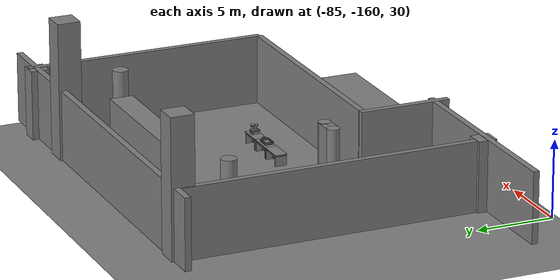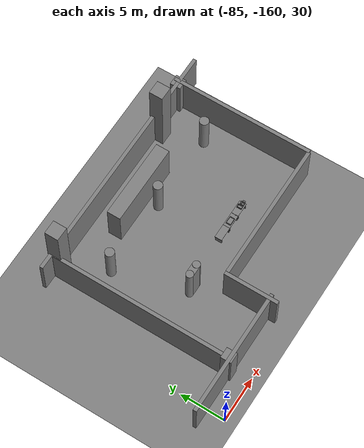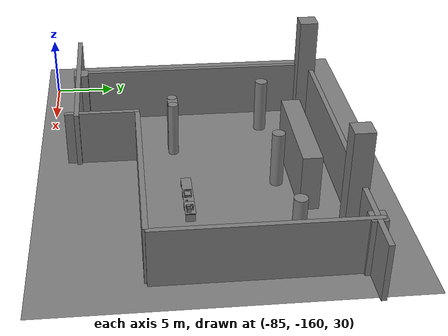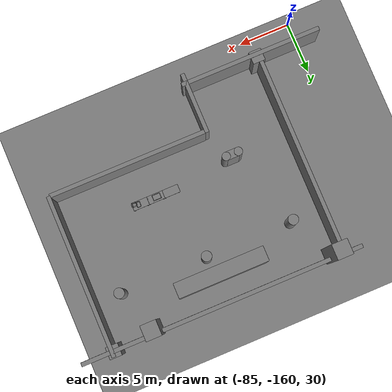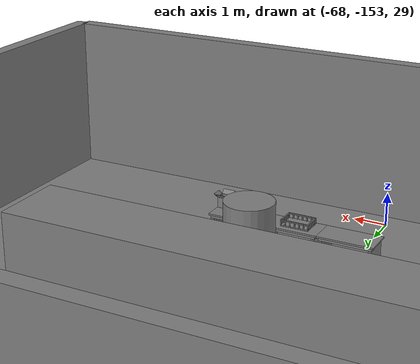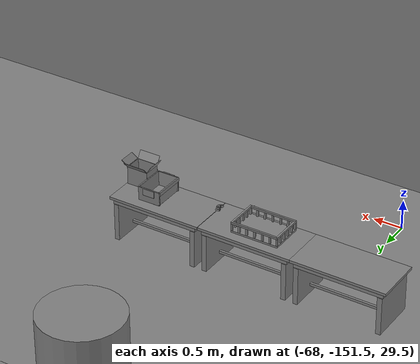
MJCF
<mujoco>
    <option gravity="0.000000000 0.000000000 -9.810000420" timestep="0.0049999999" integrator="implicitfast" density="1.225" viscosity="1.8000001e-05" noslip_iterations="10" iterations="100" sdf_iterations="50">
        <flag multiccd="disable"/>
    </option>
    <size memory="1000M"/>
    <compiler coordinate="local"/>
    <worldbody>
        <light cutoff="30" pos="0 1 1" dir="0 -1 -2"/>
        <light cutoff="30" pos="0 -1 1" dir="0 1 -2"/>
        <body pos="-64.866622925 -149.383972168 30.183746338" euler="89.999992371 89.999946594 0.000000000" name="openloong_gripper_2f85_fix_base_usda_bluebox_01">
            <geom contype="1" conaffinity="1" density="1000" type="box" material="" rgba="0.500000000 0.500000000 0.500000000 1.000000000" solimp="0.899999976 0.949999988 0.001000000" friction="1.000000000 0.005000000 0.000100000" solref="0.020000000 1.000000000" margin="0" condim="3" group="0" pos="0.276596069 0.187225342 0.000061035" quat="0.707107008 0.000077501 0.707106471 0.000077456" size="0.100000001 0.057999998 0.010000000" name="openloong_gripper_2f85_fix_base_usda_geom_1BA5A6B0_7343_43AF_AEFE_876F10B1DAE3"/>
            <geom contype="1" conaffinity="1" density="1000" type="box" material="" rgba="0.500000000 0.500000000 0.500000000 1.000000000" solimp="0.899999976 0.949999988 0.001000000" friction="1.000000000 0.005000000 0.000100000" solref="0.020000000 1.000000000" margin="0" condim="3" group="0" pos="0.000000000 0.002883911 0.000000000" quat="1.000000000 0.000000000 0.000000000 0.000000000" size="0.254000008 0.003000000 0.172000006" name="openloong_gripper_2f85_fix_base_usda_geom_FDEACEA7_01FD_449B_8E77_3979F74525C6"/>
            <geom contype="1" conaffinity="1" density="1000" type="box" material="" rgba="0.500000000 0.500000000 0.500000000 1.000000000" solimp="0.899999976 0.949999988 0.001000000" friction="1.000000000 0.005000000 0.000100000" solref="0.020000000 1.000000000" margin="0" condim="3" group="0" pos="0.000015259 0.124874115 0.173477173" quat="0.999796450 0.020176515 -0.000000015 0.000000030" size="0.259999990 0.119999997 0.007000000" name="openloong_gripper_2f85_fix_base_usda_geom_590B1DAC_7908_45C3_BE2F_CEF770CDF41E"/>
            <geom contype="1" conaffinity="1" density="1000" type="box" material="" rgba="0.500000000 0.500000000 0.500000000 1.000000000" solimp="0.899999976 0.949999988 0.001000000" friction="1.000000000 0.005000000 0.000100000" solref="0.020000000 1.000000000" margin="0" condim="3" group="0" pos="0.000015259 0.124874115 -0.173477173" quat="0.999796450 -0.020176545 -0.000000015 0.000000000" size="0.259999990 0.119999997 0.007000000" name="openloong_gripper_2f85_fix_base_usda_geom_89142A72_51AC_4546_8E6B_DD0DE406CF54"/>
            <geom contype="1" conaffinity="1" density="1000" type="box" material="" rgba="0.500000000 0.500000000 0.500000000 1.000000000" solimp="0.899999976 0.949999988 0.001000000" friction="1.000000000 0.005000000 0.000100000" solref="0.020000000 1.000000000" margin="0" condim="3" group="0" pos="0.000015259 0.214012146 0.188980103" quat="0.999913096 0.013176724 0.000000015 0.000000000" size="0.259999990 0.029999999 0.012500000" name="openloong_gripper_2f85_fix_base_usda_geom_0ADD1433_83E6_4A68_90F1_7B4438BD75CA"/>
            <geom contype="1" conaffinity="1" density="1000" type="box" material="" rgba="0.500000000 0.500000000 0.500000000 1.000000000" solimp="0.899999976 0.949999988 0.001000000" friction="1.000000000 0.005000000 0.000100000" solref="0.020000000 1.000000000" margin="0" condim="3" group="0" pos="-0.258346558 0.125289917 0.001876831" quat="0.702796996 -0.020792052 0.710783184 0.020769238" size="0.189999998 0.119999997 0.009000000" name="openloong_gripper_2f85_fix_base_usda_geom_E3080875_9E45_4B0C_9832_C8357BE8C34D"/>
            <geom contype="1" conaffinity="1" density="1000" type="box" material="" rgba="0.500000000 0.500000000 0.500000000 1.000000000" solimp="0.899999976 0.949999988 0.001000000" friction="1.000000000 0.005000000 0.000100000" solref="0.020000000 1.000000000" margin="0" condim="3" group="0" pos="0.000015259 0.214012146 -0.188980103" quat="0.999913096 -0.013176769 0.000000030 0.000000015" size="0.259999990 0.029999999 0.012500000" name="openloong_gripper_2f85_fix_base_usda_geom_4CF217C4_DBAC_4648_8597_B1141EEA98ED"/>
            <geom contype="1" conaffinity="1" density="1000" type="box" material="" rgba="0.500000000 0.500000000 0.500000000 1.000000000" solimp="0.899999976 0.949999988 0.001000000" friction="1.000000000 0.005000000 0.000100000" solref="0.020000000 1.000000000" margin="0" condim="3" group="0" pos="-0.276596069 0.187225342 0.000061035" quat="0.707106650 0.000077441 0.707106709 0.000077456" size="0.100000001 0.057999998 0.010000000" name="openloong_gripper_2f85_fix_base_usda_geom_322B87FC_FF87_4CF5_A05E_4ABAEF76EAE1"/>
            <geom contype="1" conaffinity="1" density="1000" type="box" material="" rgba="0.500000000 0.500000000 0.500000000 1.000000000" solimp="0.899999976 0.949999988 0.001000000" friction="1.000000000 0.005000000 0.000100000" solref="0.020000000 1.000000000" margin="0" condim="3" group="0" pos="0.258346558 0.125289917 0.001876831" quat="0.702851534 0.018856451 0.710823834 -0.019329429" size="0.189999998 0.119999997 0.009000000" name="openloong_gripper_2f85_fix_base_usda_geom_AC3ADFFE_963F_427B_91B8_417A8F336363"/>
            <freejoint name="openloong_gripper_2f85_fix_base_usda_bluebox_01_joint"/>
            <site size="0.005000000 0.005000000 0.005000000" rgba="0.500000000 0.500000000 0.500000000 1.000000000" pos="0.000000000 0.000000000 0.000000000" quat="0.999961913 0.008726534 0.000000000 0.000000000" group="0" type="sphere" name="openloong_gripper_2f85_fix_base_usda_bluebox_01site"/>
        </body>
        <body pos="-64.496299744 -149.491867065 30.235729218" euler="0.000000000 0.000000000 89.999946594" name="openloong_gripper_2f85_fix_base_usda_cardboardbox_01">
            <geom contype="1" conaffinity="1" density="1000" type="box" material="" rgba="0.500000000 0.500000000 0.500000000 1.000000000" solimp="0.899999976 0.949999988 0.001000000" friction="1.000000000 0.005000000 0.000100000" solref="0.020000000 1.000000000" margin="0" condim="3" group="0" pos="-0.003166199 -0.004086494 0.005052090" quat="1.000000000 0.000000000 0.000000000 0.000000000" size="0.142499998 0.177500010 0.005000000" name="openloong_gripper_2f85_fix_base_usda_geom_5E42F0DD_3BDC_4FA6_BA4A_73B70C15D10E"/>
            <geom contype="1" conaffinity="1" density="1000" type="box" material="" rgba="0.500000000 0.500000000 0.500000000 1.000000000" solimp="0.899999976 0.949999988 0.001000000" friction="1.000000000 0.005000000 0.000100000" solref="0.020000000 1.000000000" margin="0" condim="3" group="0" pos="-0.003166199 0.170316696 0.150570869" quat="1.000000000 0.000000000 0.000000000 0.000000000" size="0.142499998 0.005000000 0.149999991" name="openloong_gripper_2f85_fix_base_usda_geom_099D85C5_F57B_45F5_BB60_2A4C4876C07D"/>
            <geom contype="1" conaffinity="1" density="1000" type="box" material="" rgba="0.500000000 0.500000000 0.500000000 1.000000000" solimp="0.899999976 0.949999988 0.001000000" friction="1.000000000 0.005000000 0.000100000" solref="0.020000000 1.000000000" margin="0" condim="3" group="0" pos="-0.147399902 -0.005307198 0.150570869" quat="1.000000000 0.000000000 0.000000000 0.000000000" size="0.005000000 0.177500010 0.149999991" name="openloong_gripper_2f85_fix_base_usda_geom_A39F74C2_C695_4F74_9B2F_28A32283495F"/>
            <geom contype="1" conaffinity="1" density="1000" type="box" material="" rgba="0.500000000 0.500000000 0.500000000 1.000000000" solimp="0.899999976 0.949999988 0.001000000" friction="1.000000000 0.005000000 0.000100000" solref="0.020000000 1.000000000" margin="0" condim="3" group="0" pos="0.140275955 -0.005307198 0.150570869" quat="1.000000000 0.000000000 0.000000000 0.000000000" size="0.005000000 0.177500010 0.149999991" name="openloong_gripper_2f85_fix_base_usda_geom_761C8C02_2ECC_4527_AF38_218A2AF3CF9A"/>
            <geom contype="1" conaffinity="1" density="1000" type="box" material="" rgba="0.500000000 0.500000000 0.500000000 1.000000000" solimp="0.899999976 0.949999988 0.001000000" friction="1.000000000 0.005000000 0.000100000" solref="0.020000000 1.000000000" margin="0" condim="3" group="0" pos="-0.003166199 -0.181550980 0.150570869" quat="1.000000000 0.000000000 0.000000000 0.000000000" size="0.142499998 0.005000000 0.149999991" name="openloong_gripper_2f85_fix_base_usda_geom_AD361A9C_7CC3_405A_BF51_96282C074F85"/>
            <freejoint name="openloong_gripper_2f85_fix_base_usda_cardboardbox_01_joint"/>
            <site size="0.005000000 0.005000000 0.005000000" rgba="0.500000000 0.500000000 0.500000000 1.000000000" pos="0.000000000 0.000000000 0.000000000" quat="0.999961913 0.008726535 0.000000000 0.000000000" group="0" type="sphere" name="openloong_gripper_2f85_fix_base_usda_site_EDCD0B7B_1905_468B_AAC4_A5AB1029B60B"/>
            <body pos="0.139160156 -0.004048347 0.301930904" euler="-179.999954224 49.383502960 179.999954224" name="openloong_gripper_2f85_fix_base_usda_A1_006">
                <geom contype="1" conaffinity="1" density="1000" type="box" material="" rgba="0.500000000 0.500000000 0.500000000 1.000000000" solimp="0.899999976 0.949999988 0.001000000" friction="1.000000000 0.005000000 0.000100000" solref="0.020000000 1.000000000" margin="0" condim="3" group="0" pos="-0.071587563 0.000009537 0.001745224" quat="0.999999881 0.000000000 0.000000000 0.000000000" size="0.071249999 0.179999992 0.002500000" name="openloong_gripper_2f85_fix_base_usda_geom_CEDF62DC_1FB4_4DCC_B9CD_980BA4093E8D"/>
                <joint armature="0" stiffness="0.07" damping="0.0099999998" axis="0.000000 1.000000 0.000000" type="hinge" name="openloong_gripper_2f85_fix_base_usda_A1_006"/>
            </body>
            <body pos="-0.145902634 -0.004086494 0.301938057" euler="-180.000000000 -60.000011444 -180.000000000" name="openloong_gripper_2f85_fix_base_usda_A2_006">
                <geom contype="1" conaffinity="1" density="1000" type="box" material="" rgba="0.500000000 0.500000000 0.500000000 1.000000000" solimp="0.899999976 0.949999988 0.001000000" friction="1.000000000 0.005000000 0.000100000" solref="0.020000000 1.000000000" margin="0" condim="3" group="0" pos="0.071268082 0.000009537 0.002717972" quat="0.000002921 0.000000000 -0.000000030 0.999999881" size="0.071249999 0.179999992 0.002500000" name="openloong_gripper_2f85_fix_base_usda_geom_D158678A_0369_4A36_B267_397CB3F95B0D"/>
                <joint armature="0" stiffness="0.07" damping="0.0099999998" axis="0.000000 1.000000 0.000000" type="hinge" name="openloong_gripper_2f85_fix_base_usda_A2_006"/>
            </body>
            <body pos="-0.003385544 0.175991058 0.301930904" euler="-125.858116150 -0.000004561 0.000002331" name="openloong_gripper_2f85_fix_base_usda_B2_006">
                <geom contype="1" conaffinity="1" density="1000" type="box" material="" rgba="0.500000000 0.500000000 0.500000000 1.000000000" solimp="0.899999976 0.949999988 0.001000000" friction="1.000000000 0.005000000 0.000100000" solref="0.020000000 1.000000000" margin="0" condim="3" group="0" pos="0.000009537 -0.070939064 -0.002470016" quat="0.999614120 0.027776197 -0.000000015 0.000000030" size="0.137500003 0.064999998 0.005000000" name="openloong_gripper_2f85_fix_base_usda_geom_0A177483_D976_4364_B6B2_C84890F369AC"/>
                <joint armature="0" stiffness="0.07" damping="0.0099999998" axis="1.000000 0.000000 0.000000" type="hinge" name="openloong_gripper_2f85_fix_base_usda_B2_006"/>
            </body>
            <body pos="-0.003385544 -0.184140205 0.301938057" euler="147.805557251 0.000000000 0.000000000" name="openloong_gripper_2f85_fix_base_usda_B1_006">
                <geom contype="1" conaffinity="1" density="1000" type="box" material="" rgba="0.500000000 0.500000000 0.500000000 1.000000000" solimp="0.899999976 0.949999988 0.001000000" friction="1.000000000 0.005000000 0.000100000" solref="0.020000000 1.000000000" margin="0" condim="3" group="0" pos="-0.000028610 0.070202351 -0.002703667" quat="0.999614179 -0.027776167 0.000000000 0.000000000" size="0.137500003 0.064999998 0.005000000" name="openloong_gripper_2f85_fix_base_usda_geom_68733A8F_3D4A_4EF0_9FFF_3BD970AB1F23"/>
                <joint armature="0" stiffness="0.07" damping="0.0099999998" axis="1.000000 0.000000 0.000000" type="hinge" name="openloong_gripper_2f85_fix_base_usda_B1_006"/>
            </body>
        </body>
        <body pos="-65.882858276 -149.481979370 30.229999542" euler="-64.487716675 0.000000000 0.000000000" name="openloong_gripper_2f85_fix_base_usda_Barcode">
            <geom contype="1" conaffinity="1" density="1000" type="box" material="" rgba="0.500000000 0.500000000 0.500000000 1.000000000" solimp="0.899999976 0.949999988 0.001000000" friction="1.000000000 0.005000000 0.000100000" solref="0.020000000 1.000000000" margin="0" condim="3" group="0" pos="0.000000000 0.013038635 0.001419067" quat="0.000000000 0.000000000 0.000000000 1.000000119" size="0.034000002 0.010000000 0.017999999" name="openloong_gripper_2f85_fix_base_usda_geom_8636EC2D_23AE_47B3_A8E7_4B1E272572EC"/>
            <geom contype="1" conaffinity="1" density="1000" type="box" material="" rgba="0.500000000 0.500000000 0.500000000 1.000000000" solimp="0.899999976 0.949999988 0.001000000" friction="1.000000000 0.005000000 0.000100000" solref="0.020000000 1.000000000" margin="0" condim="3" group="0" pos="0.000000000 -0.035301208 -0.007095337" quat="0.000000000 0.000000000 -0.043619365 0.999048233" size="0.028999999 0.010000000 0.020000000" name="openloong_gripper_2f85_fix_base_usda_geom_DA4EF1A1_F3FF_44E7_944B_D48041E40EBF"/>
            <geom contype="1" conaffinity="1" density="1000" type="box" material="" rgba="0.500000000 0.500000000 0.500000000 1.000000000" solimp="0.899999976 0.949999988 0.001000000" friction="1.000000000 0.005000000 0.000100000" solref="0.020000000 1.000000000" margin="0" condim="3" group="0" pos="0.000000000 -0.043411255 -0.011749268" quat="0.922262907 0.386563420 0.000000000 0.000000000" size="0.026000001 0.010000000 0.020000000" name="openloong_gripper_2f85_fix_base_usda_geom_B3AF10D0_BFBB_4021_BA92_D425DA4C3610"/>
            <geom contype="1" conaffinity="1" density="1000" type="box" material="" rgba="0.500000000 0.500000000 0.500000000 1.000000000" solimp="0.899999976 0.949999988 0.001000000" friction="1.000000000 0.005000000 0.000100000" solref="0.020000000 1.000000000" margin="0" condim="3" group="0" pos="0.000000000 -0.016967773 -0.031860352" quat="0.000000000 0.000000000 0.000000000 1.000000119" size="0.008000000 0.010000000 0.013000000" name="openloong_gripper_2f85_fix_base_usda_geom_762145B0_B680_4446_B401_8C3357CAD987"/>
            <geom contype="1" conaffinity="1" density="1000" type="box" material="" rgba="0.500000000 0.500000000 0.500000000 1.000000000" solimp="0.899999976 0.949999988 0.001000000" friction="1.000000000 0.005000000 0.000100000" solref="0.020000000 1.000000000" margin="0" condim="3" group="0" pos="0.000000000 -0.001869202 0.000312805" quat="0.953716993 0.300705761 0.000000000 0.000000000" size="0.032000002 0.010000000 0.018999999" name="openloong_gripper_2f85_fix_base_usda_geom_ABEAA41F_5088_451B_B225_68BB449856D8"/>
            <geom contype="1" conaffinity="1" density="1000" type="box" material="" rgba="0.500000000 0.500000000 0.500000000 1.000000000" solimp="0.899999976 0.949999988 0.001000000" friction="1.000000000 0.005000000 0.000100000" solref="0.020000000 1.000000000" margin="0" condim="3" group="0" pos="0.000000000 -0.019531250 -0.003173828" quat="0.953716993 0.300705761 0.000000000 0.000000000" size="0.030999999 0.010000000 0.020000000" name="openloong_gripper_2f85_fix_base_usda_geom_4B3F118E_8585_486D_A19F_61C8CAB98EF1"/>
            <geom contype="1" conaffinity="1" density="1000" type="box" material="" rgba="0.500000000 0.500000000 0.500000000 1.000000000" solimp="0.899999976 0.949999988 0.001000000" friction="1.000000000 0.005000000 0.000100000" solref="0.020000000 1.000000000" margin="0" condim="3" group="0" pos="0.000000000 -0.035301208 -0.007095337" quat="0.953716993 0.300705761 0.000000000 0.000000000" size="0.028999999 0.010000000 0.020000000" name="openloong_gripper_2f85_fix_base_usda_geom_CC60B828_DCE9_4F59_A775_6A5E36081DC9"/>
            <geom contype="1" conaffinity="1" density="1000" type="box" material="" rgba="0.500000000 0.500000000 0.500000000 1.000000000" solimp="0.899999976 0.949999988 0.001000000" friction="1.000000000 0.005000000 0.000100000" solref="0.020000000 1.000000000" margin="0" condim="3" group="0" pos="0.000000000 -0.042617798 -0.071121216" quat="0.000000000 0.000000000 0.000000000 1.000000119" size="0.013000000 0.021000000 0.059999999" name="openloong_gripper_2f85_fix_base_usda_geom_E147D0DD_855C_4039_AFBC_42FEF404AFD2"/>
            <freejoint name="openloong_gripper_2f85_fix_base_usda_Barcode_joint"/>
            <site size="0.005000000 0.005000000 0.005000000" rgba="0.500000000 0.500000000 0.500000000 1.000000000" pos="0.000000000 0.000000000 0.000000000" quat="1.000000000 0.000000000 0.000000000 0.000000000" group="0" type="sphere" name="openloong_gripper_2f85_fix_base_usda_Barcode_site"/>
        </body>
        <body pos="-66.745018005 -149.392349243 30.184000015" euler="0.000000000 0.000000000 89.999946594" name="[22330846731095]_Basket_01">
            <geom contype="1" conaffinity="1" density="1000" type="box" material="" rgba="0.500000000 0.500000000 0.500000000 1.000000000" solimp="0.899999976 0.949999988 0.001000000" friction="1.000000000 0.005000000 0.000100000" solref="0.020000000 1.000000000" margin="0" condim="3" group="0" pos="-0.052425385 0.389207840 0.089787483" quat="0.707107008 0.000000000 0.000000000 0.707106411" size="0.014249999 0.014249999 0.059999999" name="[22330846731095]_geom_CE8924A5_5C70_4611_9777_696574319143"/>
            <geom contype="1" conaffinity="1" density="1000" type="box" material="" rgba="0.500000000 0.500000000 0.500000000 1.000000000" solimp="0.899999976 0.949999988 0.001000000" friction="1.000000000 0.005000000 0.000100000" solref="0.020000000 1.000000000" margin="0" condim="3" group="0" pos="0.264015198 -0.133043289 0.089787483" quat="0.707107008 0.000000000 0.000000000 0.707106411" size="0.014249999 0.014249999 0.059999999" name="[22330846731095]_geom_0C23460B_9106_4BA2_8882_9F07B57E898C"/>
            <geom contype="1" conaffinity="1" density="1000" type="box" material="" rgba="0.500000000 0.500000000 0.500000000 1.000000000" solimp="0.899999976 0.949999988 0.001000000" friction="1.000000000 0.005000000 0.000100000" solref="0.020000000 1.000000000" margin="0" condim="3" group="0" pos="-0.264015198 -0.265548706 0.089793205" quat="0.707107008 0.000000000 0.000000000 0.707106411" size="0.014249999 0.014249999 0.059999999" name="[22330846731095]_geom_621CFCF5_78FD_4B4C_9D07_BD9D511A1C8A"/>
            <geom contype="1" conaffinity="1" density="1000" type="box" material="" rgba="0.500000000 0.500000000 0.500000000 1.000000000" solimp="0.899999976 0.949999988 0.001000000" friction="1.000000000 0.005000000 0.000100000" solref="0.020000000 1.000000000" margin="0" condim="3" group="0" pos="-0.160263062 -0.389322281 0.089793205" quat="0.707107008 0.000000000 0.000000000 0.707106411" size="0.014249999 0.014249999 0.059999999" name="[22330846731095]_geom_E361BA86_98A7_46CD_B41E_B014C97C6355"/>
            <geom contype="1" conaffinity="1" density="1000" type="box" material="" rgba="0.500000000 0.500000000 0.500000000 1.000000000" solimp="0.899999976 0.949999988 0.001000000" friction="1.000000000 0.005000000 0.000100000" solref="0.020000000 1.000000000" margin="0" condim="3" group="0" pos="0.162265778 -0.389322281 0.089787483" quat="0.707107008 0.000000000 0.000000000 0.707106411" size="0.014249999 0.014249999 0.059999999" name="[22330846731095]_geom_5BEF2F2F_DA45_4AF7_832D_7C13765FDF09"/>
            <geom contype="1" conaffinity="1" density="1000" type="box" material="" rgba="0.500000000 0.500000000 0.500000000 1.000000000" solimp="0.899999976 0.949999988 0.001000000" friction="1.000000000 0.005000000 0.000100000" solref="0.020000000 1.000000000" margin="0" condim="3" group="0" pos="0.264015198 0.389207840 0.089787483" quat="0.707107008 0.000000000 0.000000000 0.707106411" size="0.014249999 0.014249999 0.059999999" name="[22330846731095]_geom_C508D5FF_7631_490F_A08A_91FE7A2358B1"/>
            <geom contype="1" conaffinity="1" density="1000" type="box" material="" rgba="0.500000000 0.500000000 0.500000000 1.000000000" solimp="0.899999976 0.949999988 0.001000000" friction="1.000000000 0.005000000 0.000100000" solref="0.020000000 1.000000000" margin="0" condim="3" group="0" pos="-0.264015198 -0.133043289 0.089793205" quat="0.707107008 0.000000000 0.000000000 0.707106411" size="0.014249999 0.014249999 0.059999999" name="[22330846731095]_geom_34880214_FD28_43DE_86C9_8C19DF2737A7"/>
            <geom contype="1" conaffinity="1" density="1000" type="box" material="" rgba="0.500000000 0.500000000 0.500000000 1.000000000" solimp="0.899999976 0.949999988 0.001000000" friction="1.000000000 0.005000000 0.000100000" solref="0.020000000 1.000000000" margin="0" condim="3" group="0" pos="-0.264026642 0.269256592 0.089793205" quat="0.707107008 0.000000000 0.000000000 0.707106411" size="0.014249999 0.014249999 0.059999999" name="[22330846731095]_geom_590D7781_DE44_4E7F_A841_2B74D5ED24E9"/>
            <geom contype="1" conaffinity="1" density="1000" type="box" material="" rgba="0.500000000 0.500000000 0.500000000 1.000000000" solimp="0.899999976 0.949999988 0.001000000" friction="1.000000000 0.005000000 0.000100000" solref="0.020000000 1.000000000" margin="0" condim="3" group="0" pos="0.054462433 0.389207840 0.089787483" quat="0.707107008 0.000000000 0.000000000 0.707106411" size="0.014249999 0.014249999 0.059999999" name="[22330846731095]_geom_744B595F_492E_4FE2_95C2_A1AF867954BC"/>
            <geom contype="1" conaffinity="1" density="1000" type="box" material="" rgba="0.500000000 0.500000000 0.500000000 1.000000000" solimp="0.899999976 0.949999988 0.001000000" friction="1.000000000 0.005000000 0.000100000" solref="0.020000000 1.000000000" margin="0" condim="3" group="0" pos="0.054462433 -0.389322281 0.089787483" quat="0.707107008 0.000000000 0.000000000 0.707106411" size="0.014249999 0.014249999 0.059999999" name="[22330846731095]_geom_B606E948_6F9F_4507_A722_BD30D12666A7"/>
            <geom contype="1" conaffinity="1" density="1000" type="box" material="" rgba="0.500000000 0.500000000 0.500000000 1.000000000" solimp="0.899999976 0.949999988 0.001000000" friction="1.000000000 0.005000000 0.000100000" solref="0.020000000 1.000000000" margin="0" condim="3" group="0" pos="0.264015198 0.269256592 0.089793205" quat="0.707107008 0.000000000 0.000000000 0.707106411" size="0.014249999 0.014249999 0.059999999" name="[22330846731095]_geom_D3829F3C_CBA6_4CDE_8CEA_5802E32D7D2C"/>
            <geom contype="1" conaffinity="1" density="1000" type="box" material="" rgba="0.500000000 0.500000000 0.500000000 1.000000000" solimp="0.899999976 0.949999988 0.001000000" friction="1.000000000 0.005000000 0.000100000" solref="0.020000000 1.000000000" margin="0" condim="3" group="0" pos="0.264015198 -0.389322281 0.089787483" quat="0.707107008 0.000000000 0.000000000 0.707106411" size="0.014249999 0.014249999 0.059999999" name="[22330846731095]_geom_0A31D0BB_2507_41A8_855A_EFA5E61AE97A"/>
            <geom contype="1" conaffinity="1" density="1000" type="box" material="" rgba="0.500000000 0.500000000 0.500000000 1.000000000" solimp="0.899999976 0.949999988 0.001000000" friction="1.000000000 0.005000000 0.000100000" solref="0.020000000 1.000000000" margin="0" condim="3" group="0" pos="0.000000000 0.000000000 0.015998840" quat="0.707107008 0.000000000 0.000000000 0.707106411" size="0.403499991 0.279000014 0.015750000" name="[22330846731095]_geom_C41203FB_7861_4671_8F83_D6A3905C112E"/>
            <geom contype="1" conaffinity="1" density="1000" type="box" material="" rgba="0.500000000 0.500000000 0.500000000 1.000000000" solimp="0.899999976 0.949999988 0.001000000" friction="1.000000000 0.005000000 0.000100000" solref="0.020000000 1.000000000" margin="0" condim="3" group="0" pos="0.000000000 -0.389476776 0.163619041" quat="0.707107008 0.000000000 0.000000000 0.707106411" size="0.015000000 0.277500004 0.015750000" name="[22330846731095]_geom_95D66504_7A38_44A6_ADE8_C03BA52DB28A"/>
            <geom contype="1" conaffinity="1" density="1000" type="box" material="" rgba="0.500000000 0.500000000 0.500000000 1.000000000" solimp="0.899999976 0.949999988 0.001000000" friction="1.000000000 0.005000000 0.000100000" solref="0.020000000 1.000000000" margin="0" condim="3" group="0" pos="0.162265778 0.389207840 0.089787483" quat="0.707107008 0.000000000 0.000000000 0.707106411" size="0.014249999 0.014249999 0.059999999" name="[22330846731095]_geom_A005EF91_30ED_46EC_A028_482E9A9D4BAA"/>
            <geom contype="1" conaffinity="1" density="1000" type="box" material="" rgba="0.500000000 0.500000000 0.500000000 1.000000000" solimp="0.899999976 0.949999988 0.001000000" friction="1.000000000 0.005000000 0.000100000" solref="0.020000000 1.000000000" margin="0" condim="3" group="0" pos="0.000000000 0.389471054 0.163619041" quat="0.707107008 0.000000000 0.000000000 0.707106411" size="0.015000000 0.277500004 0.015750000" name="[22330846731095]_geom_B3E287F0_F9E3_489C_83E2_75FAF54441A6"/>
            <geom contype="1" conaffinity="1" density="1000" type="box" material="" rgba="0.500000000 0.500000000 0.500000000 1.000000000" solimp="0.899999976 0.949999988 0.001000000" friction="1.000000000 0.005000000 0.000100000" solref="0.020000000 1.000000000" margin="0" condim="3" group="0" pos="-0.263511658 0.000000000 0.163619041" quat="0.707107008 0.000000000 0.000000000 0.707106411" size="0.403499991 0.015000000 0.015750000" name="[22330846731095]_geom_CD6E7B53_7A59_45ED_A7A0_3381F8064682"/>
            <geom contype="1" conaffinity="1" density="1000" type="box" material="" rgba="0.500000000 0.500000000 0.500000000 1.000000000" solimp="0.899999976 0.949999988 0.001000000" friction="1.000000000 0.005000000 0.000100000" solref="0.020000000 1.000000000" margin="0" condim="3" group="0" pos="-0.264015198 0.141334534 0.089793205" quat="0.707107008 0.000000000 0.000000000 0.707106411" size="0.014249999 0.014249999 0.059999999" name="[22330846731095]_geom_24743442_198F_4AB7_B0AB_A4FA4CC966EF"/>
            <geom contype="1" conaffinity="1" density="1000" type="box" material="" rgba="0.500000000 0.500000000 0.500000000 1.000000000" solimp="0.899999976 0.949999988 0.001000000" friction="1.000000000 0.005000000 0.000100000" solref="0.020000000 1.000000000" margin="0" condim="3" group="0" pos="0.264015198 -0.265548706 0.089787483" quat="0.707107008 0.000000000 0.000000000 0.707106411" size="0.014249999 0.014249999 0.059999999" name="[22330846731095]_geom_FE3EF369_B5E7_4D37_8904_DCE28A7DCB2F"/>
            <geom contype="1" conaffinity="1" density="1000" type="box" material="" rgba="0.500000000 0.500000000 0.500000000 1.000000000" solimp="0.899999976 0.949999988 0.001000000" friction="1.000000000 0.005000000 0.000100000" solref="0.020000000 1.000000000" margin="0" condim="3" group="0" pos="-0.160263062 0.389207840 0.089787483" quat="0.707107008 0.000000000 0.000000000 0.707106411" size="0.014249999 0.014249999 0.059999999" name="[22330846731095]_geom_F2E2786A_B57D_4F03_8ADA_B16258E6D43C"/>
            <geom contype="1" conaffinity="1" density="1000" type="box" material="" rgba="0.500000000 0.500000000 0.500000000 1.000000000" solimp="0.899999976 0.949999988 0.001000000" friction="1.000000000 0.005000000 0.000100000" solref="0.020000000 1.000000000" margin="0" condim="3" group="0" pos="-0.052425385 -0.389322281 0.089787483" quat="0.707107008 0.000000000 0.000000000 0.707106411" size="0.014249999 0.014249999 0.059999999" name="[22330846731095]_geom_C0A313AB_53DC_4CC0_BA11_96F1C2EAB2FC"/>
            <geom contype="1" conaffinity="1" density="1000" type="box" material="" rgba="0.500000000 0.500000000 0.500000000 1.000000000" solimp="0.899999976 0.949999988 0.001000000" friction="1.000000000 0.005000000 0.000100000" solref="0.020000000 1.000000000" margin="0" condim="3" group="0" pos="-0.264026642 -0.389322281 0.089793205" quat="0.707107008 0.000000000 0.000000000 0.707106411" size="0.014249999 0.014249999 0.059999999" name="[22330846731095]_geom_73F6581F_86BE_4D94_8C57_47C288366641"/>
            <geom contype="1" conaffinity="1" density="1000" type="box" material="" rgba="0.500000000 0.500000000 0.500000000 1.000000000" solimp="0.899999976 0.949999988 0.001000000" friction="1.000000000 0.005000000 0.000100000" solref="0.020000000 1.000000000" margin="0" condim="3" group="0" pos="0.264015198 0.141334534 0.089787483" quat="0.707107008 0.000000000 0.000000000 0.707106411" size="0.014249999 0.014249999 0.059999999" name="[22330846731095]_geom_D3148522_FB92_43A2_985F_E9B9EC67EB59"/>
            <geom contype="1" conaffinity="1" density="1000" type="box" material="" rgba="0.500000000 0.500000000 0.500000000 1.000000000" solimp="0.899999976 0.949999988 0.001000000" friction="1.000000000 0.005000000 0.000100000" solref="0.020000000 1.000000000" margin="0" condim="3" group="0" pos="-0.264015198 0.389207840 0.089793205" quat="0.707107008 0.000000000 0.000000000 0.707106411" size="0.014249999 0.014249999 0.059999999" name="[22330846731095]_geom_2A335615_CBA2_40B0_AD6E_01B4D8C3F3AC"/>
            <geom contype="1" conaffinity="1" density="1000" type="box" material="" rgba="0.500000000 0.500000000 0.500000000 1.000000000" solimp="0.899999976 0.949999988 0.001000000" friction="1.000000000 0.005000000 0.000100000" solref="0.020000000 1.000000000" margin="0" condim="3" group="0" pos="0.264015198 0.004480362 0.089787483" quat="0.707107008 0.000000000 0.000000000 0.707106411" size="0.014249999 0.014249999 0.059999999" name="[22330846731095]_geom_B9969F7E_AD60_44AD_8C65_0A279D6EFDCD"/>
            <geom contype="1" conaffinity="1" density="1000" type="box" material="" rgba="0.500000000 0.500000000 0.500000000 1.000000000" solimp="0.899999976 0.949999988 0.001000000" friction="1.000000000 0.005000000 0.000100000" solref="0.020000000 1.000000000" margin="0" condim="3" group="0" pos="0.263694763 -0.000011444 0.163619041" quat="0.707107008 0.000000000 0.000000000 0.707106411" size="0.403499991 0.015000000 0.015750000" name="[22330846731095]_geom_E5DCB8D9_E4B9_4F71_9B7D_273505BF4AD2"/>
            <geom contype="1" conaffinity="1" density="1000" type="box" material="" rgba="0.500000000 0.500000000 0.500000000 1.000000000" solimp="0.899999976 0.949999988 0.001000000" friction="1.000000000 0.005000000 0.000100000" solref="0.020000000 1.000000000" margin="0" condim="3" group="0" pos="-0.264015198 0.004480362 0.089793205" quat="0.707107008 0.000000000 0.000000000 0.707106411" size="0.014249999 0.014249999 0.059999999" name="[22330846731095]_geom_A02C1C3A_FBA7_4C81_A02A_E8D5F2175391"/>
            <freejoint name="[22330846731095]_joint_7FD4746D_041F_436B_AC3D_C6E25F753E34"/>
        </body>
        <body pos="0.000000000 0.000000000 0.000000000" euler="0.000000000 0.000000000 0.000000000" name="Static Objects_Static Objects">
            <geom contype="1" conaffinity="1" density="1000" type="box" material="" rgba="0.500000000 0.500000000 0.500000000 1.000000000" solimp="0.899999976 0.949999988 0.001000000" friction="1.000000000 0.005000000 0.000100000" solref="0.020000000 1.000000000" margin="0" condim="3" group="0" pos="-67.544113159 -149.365814209 29.727830887" quat="0.500000417 0.499999970 0.499999553 0.499999970" size="0.381000012 0.319999993 0.041000001" name="Static Objects_geom_AFB78F1B_460E_4B4B_B001_9EA2CFDA6D6F"/>
            <geom contype="1" conaffinity="1" density="1000" type="box" material="" rgba="0.500000000 0.500000000 0.500000000 1.000000000" solimp="0.899999976 0.949999988 0.001000000" friction="1.000000000 0.005000000 0.000100000" solref="0.020000000 1.000000000" margin="0" condim="3" group="0" pos="-68.239501953 -149.365814209 30.086868286" quat="0.500000417 0.499999970 0.499999553 0.499999970" size="0.370999992 0.039500002 0.745000005" name="Static Objects_geom_0F2F62C7_3F37_4726_BB82_DFB1BC877FF8"/>
            <geom contype="1" conaffinity="1" density="1000" type="box" material="" rgba="0.500000000 0.500000000 0.500000000 1.000000000" solimp="0.899999976 0.949999988 0.001000000" friction="1.000000000 0.005000000 0.000100000" solref="0.020000000 1.000000000" margin="0" condim="3" group="0" pos="-68.239501953 -149.365814209 30.147235870" quat="0.500000417 0.499999970 0.499999553 0.499999970" size="0.400000006 0.022000000 0.800000012" name="Static Objects_geom_187B62D8_7FEF_4D75_8AA7_95D1DA3A217E"/>
            <geom contype="1" conaffinity="1" density="1000" type="box" material="" rgba="0.500000000 0.500000000 0.500000000 1.000000000" solimp="0.899999976 0.949999988 0.001000000" friction="1.000000000 0.005000000 0.000100000" solref="0.020000000 1.000000000" margin="0" condim="3" group="0" pos="-68.934890747 -149.365814209 29.727830887" quat="0.500000417 0.499999970 0.499999553 0.499999970" size="0.381000012 0.319999993 0.041000001" name="Static Objects_geom_56AD647B_341A_4C19_8C14_78474E771E69"/>
            <geom contype="1" conaffinity="1" density="1000" type="box" material="" rgba="0.500000000 0.500000000 0.500000000 1.000000000" solimp="0.899999976 0.949999988 0.001000000" friction="1.000000000 0.005000000 0.000100000" solref="0.020000000 1.000000000" margin="0" condim="3" group="0" pos="-68.239501953 -149.365814209 29.561563492" quat="0.500000417 0.499999970 0.499999553 0.499999970" size="0.020000000 0.022000000 0.660000026" name="Static Objects_geom_C73932AF_8E8E_4398_BF08_3830A3B3FB31"/>
            <geom contype="1" conaffinity="1" density="1000" type="box" material="" rgba="0.500000000 0.500000000 0.500000000 1.000000000" solimp="0.899999976 0.949999988 0.001000000" friction="1.000000000 0.005000000 0.000100000" solref="0.020000000 1.000000000" margin="0" condim="3" group="0" pos="-65.945671082 -149.365814209 29.727830887" quat="0.500000417 0.499999970 0.499999553 0.499999970" size="0.381000012 0.319999993 0.041000001" name="Static Objects_geom_37D9D242_830F_4E3D_A570_DE779801D61E"/>
            <geom contype="1" conaffinity="1" density="1000" type="box" material="" rgba="0.500000000 0.500000000 0.500000000 1.000000000" solimp="0.899999976 0.949999988 0.001000000" friction="1.000000000 0.005000000 0.000100000" solref="0.020000000 1.000000000" margin="0" condim="3" group="0" pos="-66.641059875 -149.365814209 30.086868286" quat="0.500000417 0.499999970 0.499999553 0.499999970" size="0.370999992 0.039500002 0.745000005" name="Static Objects_geom_571475D6_9E2F_4332_90FF_B063FF7D6AAC"/>
            <geom contype="1" conaffinity="1" density="1000" type="box" material="" rgba="0.500000000 0.500000000 0.500000000 1.000000000" solimp="0.899999976 0.949999988 0.001000000" friction="1.000000000 0.005000000 0.000100000" solref="0.020000000 1.000000000" margin="0" condim="3" group="0" pos="-66.641059875 -149.365814209 30.147235870" quat="0.500000417 0.499999970 0.499999553 0.499999970" size="0.400000006 0.022000000 0.800000012" name="Static Objects_geom_03464499_1F7C_4BFF_AB41_905EBB4F79AB"/>
            <geom contype="1" conaffinity="1" density="1000" type="box" material="" rgba="0.500000000 0.500000000 0.500000000 1.000000000" solimp="0.899999976 0.949999988 0.001000000" friction="1.000000000 0.005000000 0.000100000" solref="0.020000000 1.000000000" margin="0" condim="3" group="0" pos="-67.336448669 -149.365814209 29.727830887" quat="0.500000417 0.499999970 0.499999553 0.499999970" size="0.381000012 0.319999993 0.041000001" name="Static Objects_geom_6509F6CE_8586_4816_BE48_E453C356195E"/>
            <geom contype="1" conaffinity="1" density="1000" type="box" material="" rgba="0.500000000 0.500000000 0.500000000 1.000000000" solimp="0.899999976 0.949999988 0.001000000" friction="1.000000000 0.005000000 0.000100000" solref="0.020000000 1.000000000" margin="0" condim="3" group="0" pos="-66.641059875 -149.365814209 29.561563492" quat="0.500000417 0.499999970 0.499999553 0.499999970" size="0.020000000 0.022000000 0.660000026" name="Static Objects_geom_93FFB12F_DA5F_4C96_A15C_EEFE175819AF"/>
            <geom contype="1" conaffinity="1" density="1000" type="box" material="" rgba="0.500000000 0.500000000 0.500000000 1.000000000" solimp="0.899999976 0.949999988 0.001000000" friction="1.000000000 0.005000000 0.000100000" solref="0.020000000 1.000000000" margin="0" condim="3" group="0" pos="-64.338577271 -149.365814209 29.727830887" quat="0.500000417 0.499999970 0.499999553 0.499999970" size="0.381000012 0.319999993 0.041000001" name="Static Objects_geom_D337E1E3_C3DE_4979_BCE7_404E7BC62954"/>
            <geom contype="1" conaffinity="1" density="1000" type="box" material="" rgba="0.500000000 0.500000000 0.500000000 1.000000000" solimp="0.899999976 0.949999988 0.001000000" friction="1.000000000 0.005000000 0.000100000" solref="0.020000000 1.000000000" margin="0" condim="3" group="0" pos="-65.033966064 -149.365814209 30.086868286" quat="0.500000417 0.499999970 0.499999553 0.499999970" size="0.370999992 0.039500002 0.745000005" name="Static Objects_geom_C6468644_BEEA_46FB_B21C_77AD6784B52D"/>
            <geom contype="1" conaffinity="1" density="1000" type="box" material="" rgba="0.500000000 0.500000000 0.500000000 1.000000000" solimp="0.899999976 0.949999988 0.001000000" friction="1.000000000 0.005000000 0.000100000" solref="0.020000000 1.000000000" margin="0" condim="3" group="0" pos="-65.033966064 -149.365814209 30.147235870" quat="0.500000417 0.499999970 0.499999553 0.499999970" size="0.400000006 0.022000000 0.800000012" name="Static Objects_geom_94ABB5F6_05DA_4F89_A0A0_16AA5B176432"/>
            <geom contype="1" conaffinity="1" density="1000" type="box" material="" rgba="0.500000000 0.500000000 0.500000000 1.000000000" solimp="0.899999976 0.949999988 0.001000000" friction="1.000000000 0.005000000 0.000100000" solref="0.020000000 1.000000000" margin="0" condim="3" group="0" pos="-65.729354858 -149.365814209 29.727830887" quat="0.500000417 0.499999970 0.499999553 0.499999970" size="0.381000012 0.319999993 0.041000001" name="Static Objects_geom_4D7C8FF1_0085_496E_A790_243D6401A925"/>
            <geom contype="1" conaffinity="1" density="1000" type="box" material="" rgba="0.500000000 0.500000000 0.500000000 1.000000000" solimp="0.899999976 0.949999988 0.001000000" friction="1.000000000 0.005000000 0.000100000" solref="0.020000000 1.000000000" margin="0" condim="3" group="0" pos="-65.033966064 -149.365814209 29.561563492" quat="0.500000417 0.499999970 0.499999553 0.499999970" size="0.020000000 0.022000000 0.660000026" name="Static Objects_geom_C513D092_6582_4883_9CE9_E8D82DD75F30"/>
            <geom contype="1" conaffinity="1" density="1000" type="box" material="" rgba="0.500000000 0.500000000 0.500000000 1.000000000" solimp="0.899999976 0.949999988 0.001000000" friction="1.000000000 0.005000000 0.000100000" solref="0.020000000 1.000000000" margin="0" condim="3" group="0" pos="-61.754566193 -137.853729248 33.906845093" quat="0.707107067 0.000000000 0.000000000 0.707106471" size="0.759999990 0.759999990 4.500000000" name="Static Objects_geom_A872B0DE_9FC9_4805_A2B7_DCDBA8E6C5C6"/>
            <geom contype="1" conaffinity="1" density="1000" type="box" material="" rgba="0.500000000 0.500000000 0.500000000 1.000000000" solimp="0.899999976 0.949999988 0.001000000" friction="1.000000000 0.005000000 0.000100000" solref="0.020000000 1.000000000" margin="0" condim="3" group="0" pos="-57.511135101 -144.927108765 31.707921982" quat="1.000000000 0.000000000 0.000000000 0.000000000" size="0.200000003 8.000000000 2.299999952" name="Static Objects_geom_15E9AF73_B780_4CCA_8D54_70FA22D88577"/>
            <geom contype="1" conaffinity="1" density="1000" type="box" material="" rgba="0.500000000 0.500000000 0.500000000 1.000000000" solimp="0.899999976 0.949999988 0.001000000" friction="1.000000000 0.005000000 0.000100000" solref="0.020000000 1.000000000" margin="0" condim="3" group="0" pos="-80.517646790 -157.574050903 31.688196182" quat="0.707107067 0.000000000 0.000000000 0.707106471" size="0.600000024 0.600000024 2.299999952" name="Static Objects_geom_CB36C3C0_13A1_499B_AA09_A41BA5CAA978"/>
            <geom contype="1" conaffinity="1" density="1000" type="box" material="" rgba="0.500000000 0.500000000 0.500000000 1.000000000" solimp="0.899999976 0.949999988 0.001000000" friction="1.000000000 0.005000000 0.000100000" solref="0.020000000 1.000000000" margin="0" condim="3" group="0" pos="-80.711044312 -147.414932251 31.666158676" quat="1.000000000 0.000000000 0.000000000 0.000000000" size="0.200000003 10.000000000 2.299999952" name="Static Objects_geom_07DF69D2_C38C_4377_AE4A_82E28E0E9A94"/>
            <geom contype="1" conaffinity="1" density="1000" type="box" material="" rgba="0.500000000 0.500000000 0.500000000 1.000000000" solimp="0.899999976 0.949999988 0.001000000" friction="1.000000000 0.005000000 0.000100000" solref="0.020000000 1.000000000" margin="0" condim="3" group="0" pos="-57.687217712 -137.434692383 31.688196182" quat="0.707107067 0.000000000 0.000000000 0.707106471" size="0.600000024 0.600000024 2.299999952" name="Static Objects_geom_55892867_D24A_4A01_9B9B_D3EC54D40095"/>
            <geom contype="1" conaffinity="1" density="1000" type="box" material="" rgba="0.500000000 0.500000000 0.500000000 1.000000000" solimp="0.899999976 0.949999988 0.001000000" friction="1.000000000 0.005000000 0.000100000" solref="0.020000000 1.000000000" margin="0" condim="3" group="0" pos="-69.537033081 -140.263229370 31.714921951" quat="0.707107067 0.000000000 0.000000000 0.707106471" size="0.759999990 4.500000000 2.299999952" name="Static Objects_geom_7D74B08C_30A4_4383_8078_D0934B59BC79"/>
            <geom contype="1" conaffinity="1" density="1000" type="box" material="" rgba="0.500000000 0.500000000 0.500000000 1.000000000" solimp="0.899999976 0.949999988 0.001000000" friction="1.000000000 0.005000000 0.000100000" solref="0.020000000 1.000000000" margin="0" condim="3" group="0" pos="-80.073638916 -137.853713989 33.906845093" quat="0.707107067 0.000000000 0.000000000 0.707106471" size="0.759999990 0.759999990 4.500000000" name="Static Objects_geom_B2734AEB_5773_4BB6_A05D_5DAC80880F3F"/>
            <geom contype="1" conaffinity="1" density="1000" type="box" material="" rgba="0.500000000 0.500000000 0.500000000 1.000000000" solimp="0.899999976 0.949999988 0.001000000" friction="1.000000000 0.005000000 0.000100000" solref="0.020000000 1.000000000" margin="0" condim="3" group="0" pos="-73.406707764 -155.734664917 31.707921982" quat="1.000000000 0.000000000 0.000000000 0.000000000" size="0.200000003 3.000000000 2.299999952" name="Static Objects_geom_0D3A2D04_4057_4A65_8D51_7FBBF19FBB36"/>
            <geom contype="1" conaffinity="1" density="1000" type="box" material="" rgba="0.500000000 0.500000000 0.500000000 1.000000000" solimp="0.899999976 0.949999988 0.001000000" friction="1.000000000 0.005000000 0.000100000" solref="0.020000000 1.000000000" margin="0" condim="3" group="0" pos="-68.497543335 -137.448257446 31.707921982" quat="0.707107067 0.000000000 0.000000000 0.707106471" size="0.200000003 14.000000000 2.299999952" name="Static Objects_geom_2A6ED7F6_3A31_4715_885C_188E31331F6A"/>
            <geom contype="1" conaffinity="1" density="1000" type="cylinder" material="" rgba="0.500000000 0.500000000 0.500000000 1.000000000" solimp="0.899999976 0.949999988 0.001000000" friction="1.000000000 0.005000000 0.000100000" solref="0.020000000 1.000000000" margin="0" condim="3" group="0" pos="-68.868522644 -142.134506226 31.711090088" quat="0.707107067 0.000000000 0.000000000 0.707106471" size="0.509999990 2.299999952 1.000000000" name="Static Objects_geom_089C51B3_6D68_4987_87E8_907B8FF840FA"/>
            <geom contype="1" conaffinity="1" density="1000" type="plane" material="" rgba="0.500000000 0.500000000 0.500000000 1.000000000" solimp="0.899999976 0.949999988 0.001000000" friction="1.000000000 0.005000000 0.000100000" solref="0.020000000 1.000000000" margin="0" condim="3" group="0" pos="-72.873703003 -147.131927490 29.409669876" quat="1.000000000 0.000000000 0.000000000 0.000000000" size="18.000000000 14.000000000 1.000000000" name="Static Objects_geom_9A6B3B00_4ED5_440F_A8F3_2D713AFD1A5B"/>
            <geom contype="1" conaffinity="1" density="1000" type="box" material="" rgba="0.500000000 0.500000000 0.500000000 1.000000000" solimp="0.899999976 0.949999988 0.001000000" friction="1.000000000 0.005000000 0.000100000" solref="0.020000000 1.000000000" margin="0" condim="3" group="0" pos="-79.943580627 -157.782272339 31.707921982" quat="0.707107067 0.000000000 0.000000000 0.707106471" size="0.200000003 7.000000000 2.299999952" name="Static Objects_geom_834A6638_12F8_4227_BAD8_A6A0991D4CAB"/>
            <geom contype="1" conaffinity="1" density="1000" type="box" material="" rgba="0.500000000 0.500000000 0.500000000 1.000000000" solimp="0.899999976 0.949999988 0.001000000" friction="1.000000000 0.005000000 0.000100000" solref="0.020000000 1.000000000" margin="0" condim="3" group="0" pos="-65.421028137 -152.903442383 31.707921982" quat="0.707107067 0.000000000 0.000000000 0.707106471" size="0.200000003 7.800000191 2.299999952" name="Static Objects_geom_48AF2129_8A77_4971_9112_334CF8331CB5"/>
            <geom contype="1" conaffinity="1" density="1000" type="box" material="" rgba="0.500000000 0.500000000 0.500000000 1.000000000" solimp="0.899999976 0.949999988 0.001000000" friction="1.000000000 0.005000000 0.000100000" solref="0.020000000 1.000000000" margin="0" condim="3" group="0" pos="-74.776908875 -149.964416504 31.688196182" quat="1.000000000 0.000000000 0.000000000 0.000000000" size="0.600000024 0.409999996 2.299999952" name="Static Objects_geom_90746429_9A6C_4C4C_ADAB_C0169858E75C"/>
            <geom contype="1" conaffinity="1" density="1000" type="cylinder" material="" rgba="0.500000000 0.500000000 0.500000000 1.000000000" solimp="0.899999976 0.949999988 0.001000000" friction="1.000000000 0.005000000 0.000100000" solref="0.020000000 1.000000000" margin="0" condim="3" group="0" pos="-60.161884308 -142.134506226 31.711090088" quat="0.707107067 0.000000000 0.000000000 0.707106471" size="0.509999990 2.299999952 1.000000000" name="Static Objects_geom_3B4BCD9E_809D_4761_8C68_35C8C3478A98"/>
            <geom contype="1" conaffinity="1" density="1000" type="cylinder" material="" rgba="0.500000000 0.500000000 0.500000000 1.000000000" solimp="0.899999976 0.949999988 0.001000000" friction="1.000000000 0.005000000 0.000100000" solref="0.020000000 1.000000000" margin="0" condim="3" group="0" pos="-75.382453918 -149.963455200 31.711090088" quat="0.707107067 0.000000000 0.000000000 0.707106471" size="0.409999996 2.299999952 1.000000000" name="Static Objects_geom_B02F6390_EA21_444D_9F97_46FFA2DADD9B"/>
            <geom contype="1" conaffinity="1" density="1000" type="cylinder" material="" rgba="0.500000000 0.500000000 0.500000000 1.000000000" solimp="0.899999976 0.949999988 0.001000000" friction="1.000000000 0.005000000 0.000100000" solref="0.020000000 1.000000000" margin="0" condim="3" group="0" pos="-74.154960632 -149.963455200 31.711090088" quat="0.707107067 0.000000000 0.000000000 0.707106471" size="0.409999996 2.299999952 1.000000000" name="Static Objects_geom_CA2746D8_D6EB_4208_BDAF_2A3BEAD93EAD"/>
            <geom contype="1" conaffinity="1" density="1000" type="cylinder" material="" rgba="0.500000000 0.500000000 0.500000000 1.000000000" solimp="0.899999976 0.949999988 0.001000000" friction="1.000000000 0.005000000 0.000100000" solref="0.020000000 1.000000000" margin="0" condim="3" group="0" pos="-77.566612244 -142.134506226 31.711090088" quat="0.707107067 0.000000000 0.000000000 0.707106471" size="0.509999990 2.299999952 1.000000000" name="Static Objects_geom_8D918F7C_54C0_4AC1_8DEB_8914B67B6029"/>
        </body>
        <body pos="-66.291030884 -149.869689941 29.018842697" euler="0.000000000 0.000000000 89.999946594" mocap="true" name="openloong_gripper_2f85_fix_base_usda_leftHandMocap"/>
        <body pos="-66.291030884 -149.869689941 29.018842697" euler="0.000000000 0.000000000 89.999946594" mocap="true" name="openloong_gripper_2f85_fix_base_usda_rightHandMocap"/>
        <body pos="-66.291030884 -149.869689941 30.218843460" euler="0.000000000 0.000000000 89.999946594" name="openloong_gripper_2f85_fix_base_usda_base_link">
            <geom contype="1" conaffinity="1" density="1000" type="mesh" material="" rgba="0.783999979 0.783999979 0.783999979 1.000000000" solimp="0.899999976 0.949999988 0.001000000" friction="1.000000000 0.005000000 0.000100000" solref="0.020000000 1.000000000" margin="0" condim="3" group="3" mesh="base_link" pos="0.000000000 0.000000000 0.000000000" quat="1.000000000 0.000000000 0.000000000 0.000000000" size="1.000000000 1.000000000 1.000000000" name="openloong_gripper_2f85_fix_base_usda__geom_7_77FD6AB1_63DE_4054_AA92_135D5928D487"/>
            <site size="0.005000000 0.005000000 0.005000000" rgba="0.500000000 0.500000000 0.500000000 1.000000000" pos="0.000000000 0.000000000 0.000000000" quat="1.000000000 0.000000000 0.000000000 0.000000000" group="0" type="sphere" name="openloong_gripper_2f85_fix_base_usda_imu"/>
            <inertial mass="22.447001" pos="-0.005664100 -0.001336700 0.238289997" diaginertia="0.374352545 0.277180195 0.220617250" quat="0.999247074 0.035235517 -0.015086859 0.006023135"/>
            <body pos="0.000000000 0.000000000 0.299997330" euler="0.000000000 0.000000000 0.000000000" name="openloong_gripper_2f85_fix_base_usda_dummy_body">
                <geom contype="1" conaffinity="1" density="1000" type="sphere" material="" rgba="0.783999979 0.783999979 0.783999979 1.000000000" solimp="0.899999976 0.949999988 0.001000000" friction="1.000000000 0.005000000 0.000100000" solref="0.020000000 1.000000000" margin="0" condim="3" group="3" pos="0.000000000 0.000000000 0.000000000" quat="1.000000000 0.000000000 0.000000000 0.000000000" size="0.010000000 0.000000000 0.000000000" name="openloong_gripper_2f85_fix_base_usda__geom_8_02C29637_6EA2_4F13_96BB_862EE365D2D7"/>
                <joint armature="0.0099999998" stiffness="0" damping="0.1" axis="0.000000 0.000000 1.000000" type="hinge" name="openloong_gripper_2f85_fix_base_usda_dummy_joint"/>
                <site size="0.010000000 0.005000000 0.005000000" rgba="0.500000000 0.500000000 0.500000000 1.000000000" pos="0.000000000 0.000000000 0.000000000" quat="1.000000000 0.000000000 0.000000000 0.000000000" group="3" type="sphere" name="openloong_gripper_2f85_fix_base_usda_dummy_site"/>
            </body>
            <body pos="0.009002686 0.000000000 0.406400681" euler="0.000000000 0.000000000 0.000000000" name="openloong_gripper_2f85_fix_base_usda_Link_head_yaw">
                <geom contype="1" conaffinity="1" density="1000" type="mesh" material="" rgba="0.783999979 0.783999979 0.783999979 1.000000000" solimp="0.899999976 0.949999988 0.001000000" friction="1.000000000 0.005000000 0.000100000" solref="0.020000000 1.000000000" margin="0" condim="3" group="3" mesh="Link_head_yaw" pos="0.000000000 0.000000000 0.000000000" quat="1.000000000 0.000000000 0.000000000 0.000000000" size="1.000000000 1.000000000 1.000000000" name="openloong_gripper_2f85_fix_base_usda__geom_10_801C6DB1_E0C2_4FAE_A6E6_5B09FCABB204"/>
                <inertial mass="0.84249002" pos="0.000000000 -0.002081400 0.044801001" diaginertia="0.000700588 0.000629000 0.000553812" quat="0.706933022 -0.015675601 0.015677100 0.706933022"/>
                <body pos="0.000000000 -0.034599304 0.048500061" euler="0.000000000 0.000000000 0.000000000" name="openloong_gripper_2f85_fix_base_usda_Link_head_pitch">
                    <geom contype="1" conaffinity="1" density="1000" type="mesh" material="" rgba="0.783999979 0.783999979 0.783999979 1.000000000" solimp="0.899999976 0.949999988 0.001000000" friction="1.000000000 0.005000000 0.000100000" solref="0.020000000 1.000000000" margin="0" condim="3" group="3" mesh="Link_head_pitch" pos="0.000000000 0.000000000 0.000000000" quat="1.000000000 0.000000000 0.000000000 0.000000000" size="1.000000000 1.000000000 1.000000000" name="openloong_gripper_2f85_fix_base_usda__geom_12_1D40F43A_3812_4607_99DC_DD5298EFC4FC"/>
                    <inertial mass="1.3943" pos="0.020569000 0.033004001 0.125000000" diaginertia="0.006381400 0.006289940 0.004481460" quat="0.973390222 0.008406822 0.228157058 0.019624906"/>
                    <body pos="0.000000000 0.029998779 0.000000000" euler="0.000000000 0.000000000 0.000000000" name="openloong_gripper_2f85_fix_base_usda_neck_center_body">
                        <site size="0.010000000 0.005000000 0.005000000" rgba="0.500000000 0.500000000 0.500000000 1.000000000" pos="0.000000000 0.000000000 0.000000000" quat="1.000000000 0.000000000 0.000000000 0.000000000" group="3" type="sphere" name="openloong_gripper_2f85_fix_base_usda_neck_center_site"/>
                        <body pos="0.020004272 0.000000000 0.149999619" euler="-0.000002229 39.998176575 -90.000205994" name="openloong_gripper_2f85_fix_base_usda_camera_head">
                            <site size="0.010000000 0.005000000 0.005000000" rgba="0.500000000 0.500000000 0.500000000 1.000000000" pos="0.000000000 0.000000000 0.000000000" quat="1.000000000 0.000000000 0.000000000 0.000000000" group="3" type="sphere" name="openloong_gripper_2f85_fix_base_usda_camera_head_site"/>
                        </body>
                    </body>
                </body>
            </body>
            <body pos="0.003997803 -0.161598206 0.392200470" euler="0.000000000 0.000000000 0.000000000" name="openloong_gripper_2f85_fix_base_usda_Link_arm_r_01">
                <geom contype="1" conaffinity="1" density="1000" type="mesh" material="" rgba="0.783999979 0.783999979 0.783999979 1.000000000" solimp="0.899999976 0.949999988 0.001000000" friction="1.000000000 0.005000000 0.000100000" solref="0.020000000 1.000000000" margin="0" condim="3" group="3" mesh="Link_arm_r_01" pos="0.000000000 0.000000000 0.000000000" quat="1.000000000 0.000000000 0.000000000 0.000000000" size="1.000000000 1.000000000 1.000000000" name="openloong_gripper_2f85_fix_base_usda__geom_14_E1D2F98D_6ECD_4C34_AAAA_58F1206DF03B"/>
                <joint armature="0.0099999998" stiffness="0" damping="1" axis="0.000000 -1.000000 0.000000" limited="true" range="-170.000015259 170.000015259" type="hinge" name="openloong_gripper_2f85_fix_base_usda_J_arm_r_01"/>
                <inertial mass="0.75641" pos="0.004494600 -0.038293999 -0.000001874" diaginertia="0.000842990 0.000803050 0.000587120" quat="-0.000163502 0.707098067 0.000812463 0.707115054"/>
                <body pos="-0.041992188 -0.041000366 0.000000000" euler="0.000000000 0.000000000 0.000000000" name="openloong_gripper_2f85_fix_base_usda_Link_arm_r_02">
                    <geom contype="1" conaffinity="1" density="1000" type="mesh" material="" rgba="0.783999979 0.783999979 0.783999979 1.000000000" solimp="0.899999976 0.949999988 0.001000000" friction="1.000000000 0.005000000 0.000100000" solref="0.020000000 1.000000000" margin="0" condim="3" group="3" mesh="Link_arm_r_02" pos="0.000000000 0.000000000 0.000000000" quat="1.000000000 0.000000000 0.000000000 0.000000000" size="1.000000000 1.000000000 1.000000000" name="openloong_gripper_2f85_fix_base_usda__geom_16_2EC5A572_F9BF_4473_8D7B_EE7F24DB294E"/>
                    <joint armature="0.0099999998" stiffness="0" damping="1" axis="-1.000000 0.000000 0.000000" limited="true" range="-105.000244141 105.000244141" type="hinge" name="openloong_gripper_2f85_fix_base_usda_J_arm_r_02"/>
                    <inertial mass="0.98500001" pos="0.041999999 -0.067430697 0.000000000" diaginertia="0.002262690 0.001730990 0.001154020" quat="0.500000000 0.500000000 -0.500000000 0.500000000"/>
                    <body pos="0.041992188 -0.122596741 0.000000000" euler="0.000000000 0.000000000 0.000000000" name="openloong_gripper_2f85_fix_base_usda_Link_arm_r_03">
                        <geom contype="1" conaffinity="1" density="1000" type="mesh" material="" rgba="0.783999979 0.783999979 0.783999979 1.000000000" solimp="0.899999976 0.949999988 0.001000000" friction="1.000000000 0.005000000 0.000100000" solref="0.020000000 1.000000000" margin="0" condim="3" group="3" mesh="Link_arm_r_03" pos="0.000000000 0.000000000 0.000000000" quat="1.000000000 0.000000000 0.000000000 0.000000000" size="1.000000000 1.000000000 1.000000000" name="openloong_gripper_2f85_fix_base_usda__geom_18_42FF7305_356B_4C50_B532_5CA339C7C939"/>
                        <joint armature="0.0099999998" stiffness="0" damping="1" axis="0.000000 -1.000000 0.000000" limited="true" range="-170.000015259 170.000015259" type="hinge" name="openloong_gripper_2f85_fix_base_usda_J_arm_r_03"/>
                        <inertial mass="0.95899999" pos="-0.001413580 -0.164663002 0.020757901" diaginertia="0.002101340 0.002064590 0.000754802" quat="0.560480952 0.454391927 -0.443732947 0.531497955"/>
                        <body pos="0.035293579 -0.177406311 0.023998260" euler="0.000000000 0.000000000 0.000000000" name="openloong_gripper_2f85_fix_base_usda_Link_arm_r_04">
                            <geom contype="1" conaffinity="1" density="1000" type="mesh" material="" rgba="0.783999979 0.783999979 0.783999979 1.000000000" solimp="0.899999976 0.949999988 0.001000000" friction="1.000000000 0.005000000 0.000100000" solref="0.020000000 1.000000000" margin="0" condim="3" group="3" mesh="Link_arm_r_04" pos="0.000000000 0.000000000 0.000000000" quat="1.000000000 0.000000000 0.000000000 0.000000000" size="1.000000000 1.000000000 1.000000000" name="openloong_gripper_2f85_fix_base_usda__geom_20_651F7F9A_191A_4DC9_9C40_8258E3A9F211"/>
                            <joint armature="0.0099999998" stiffness="0" damping="1" axis="-1.000000 0.000000 0.000000" limited="true" range="0.000000000 170.000015259" type="hinge" name="openloong_gripper_2f85_fix_base_usda_J_arm_r_04"/>
                            <inertial mass="0.60000002" pos="-0.038727000 -0.060766999 -0.021003000" diaginertia="0.001092610 0.000712422 0.000645102" quat="0.327701002 0.632602990 -0.467366993 0.523443997"/>
                            <body pos="-0.035293579 -0.103492737 -0.023998260" euler="0.000000000 0.000000000 0.000000000" name="openloong_gripper_2f85_fix_base_usda_Link_arm_r_05">
                                <geom contype="1" conaffinity="1" density="1000" type="mesh" material="" rgba="0.783999979 0.783999979 0.783999979 1.000000000" solimp="0.899999976 0.949999988 0.001000000" friction="1.000000000 0.005000000 0.000100000" solref="0.020000000 1.000000000" margin="0" condim="3" group="3" mesh="Link_arm_r_05" pos="0.000000000 0.000000000 0.000000000" quat="1.000000000 0.000000000 0.000000000 0.000000000" size="1.000000000 1.000000000 1.000000000" name="openloong_gripper_2f85_fix_base_usda__geom_22_B41802C1_6AA1_461A_AE8A_73AE82F9F4DF"/>
                                <joint armature="0.0099999998" stiffness="0" damping="1" axis="0.000000 -1.000000 0.000000" limited="true" range="-170.000015259 170.000015259" type="hinge" name="openloong_gripper_2f85_fix_base_usda_J_arm_r_05"/>
                                <inertial mass="0.68976003" pos="0.000032712 -0.068658002 -0.000111780" diaginertia="0.002522510 0.002411100 0.000448695" quat="0.707660973 0.706543028 -0.002603360 0.002470550"/>
                                <body pos="-0.026489258 -0.196502686 0.000000000" euler="0.000000000 0.000000000 0.000000000" name="openloong_gripper_2f85_fix_base_usda_Link_arm_r_06">
                                    <geom contype="1" conaffinity="1" density="1000" type="mesh" material="" rgba="0.783999979 0.783999979 0.783999979 1.000000000" solimp="0.899999976 0.949999988 0.001000000" friction="1.000000000 0.005000000 0.000100000" solref="0.020000000 1.000000000" margin="0" condim="3" group="3" mesh="Link_arm_r_06" pos="0.000000000 0.000000000 0.000000000" quat="1.000000000 0.000000000 0.000000000 0.000000000" size="1.000000000 1.000000000 1.000000000" name="openloong_gripper_2f85_fix_base_usda__geom_24_B840645A_E81B_4F90_A66F_ED49D1AB4B1C"/>
                                    <joint armature="0.0099999998" stiffness="0" damping="1" axis="1.000000 0.000000 0.000000" limited="true" range="-105.000244141 105.000244141" type="hinge" name="openloong_gripper_2f85_fix_base_usda_J_arm_r_06"/>
                                    <inertial mass="0.28" pos="0.026078001 -0.000000896 0.001663700" diaginertia="0.000156930 0.000145601 0.000104979" quat="0.707080841 0.001851080 0.001883810 0.707127810"/>
                                    <body pos="0.026489258 0.000000000 0.031799316" euler="0.000000000 0.000000000 0.000000000" name="openloong_gripper_2f85_fix_base_usda_Link_arm_r_07">
                                        <geom contype="1" conaffinity="1" density="1000" type="mesh" material="" rgba="0.783999979 0.783999979 0.783999979 1.000000000" solimp="0.899999976 0.949999988 0.001000000" friction="1.000000000 0.005000000 0.000100000" solref="0.020000000 1.000000000" margin="0" condim="3" group="3" mesh="Link_arm_r_07" pos="0.000000000 0.000000000 0.000000000" quat="1.000000000 0.000000000 0.000000000 0.000000000" size="1.000000000 1.000000000 1.000000000" name="openloong_gripper_2f85_fix_base_usda__geom_26_4E7FDDB6_7FFC_40B9_B602_D88FBEA6B94A"/>
                                        <joint armature="0.0099999998" stiffness="0" damping="1" axis="0.000000 0.000000 1.000000" limited="true" range="-60.000133514 60.000133514" type="hinge" name="openloong_gripper_2f85_fix_base_usda_J_arm_r_07"/>
                                        <inertial mass="0.61353999" pos="-0.007859000 -0.158170000 -0.027736001" diaginertia="0.003037610 0.002570910 0.000729379" quat="0.427542925 0.443532884 -0.553093910 0.560867906"/>
                                        <body pos="0.000000000 0.286994934 -0.270000458" euler="150.000350952 -0.000001649 -0.000000442" name="openloong_gripper_2f85_fix_base_usda_camera_wrist_r">
                                            <site size="0.010000000 0.005000000 0.005000000" rgba="0.500000000 0.500000000 0.500000000 1.000000000" pos="0.000000000 0.000000000 0.000000000" quat="1.000000000 0.000000000 0.000000000 0.000000000" group="3" type="sphere" name="openloong_gripper_2f85_fix_base_usda_camera_wrist_r_site"/>
                                        </body>
                                        <body pos="0.000000000 -0.220008850 -0.033002853" euler="0.000000000 0.000000000 179.999969482" name="openloong_gripper_2f85_fix_base_usda_ee_center_body_r">
                                            <site size="0.010000000 0.005000000 0.005000000" rgba="0.500000000 0.500000000 0.500000000 1.000000000" pos="0.000000000 0.000000000 0.000000000" quat="1.000000000 0.000000000 0.000000000 0.000000000" group="3" type="sphere" name="openloong_gripper_2f85_fix_base_usda_ee_center_site_r"/>
                                        </body>
                                        <body pos="0.000000000 -0.066001892 -0.031000137" euler="89.999984741 0.000000000 180.000000000" name="openloong_gripper_2f85_fix_base_usda_zbr_base_link">
                                            <geom contype="1" conaffinity="1" density="1000" type="mesh" material="" rgba="0.783999979 0.783999979 0.783999979 1.000000000" solimp="0.899999976 0.949999988 0.001000000" friction="1.000000000 0.005000000 0.000100000" solref="0.020000000 1.000000000" margin="0" condim="3" group="3" mesh="base" pos="0.000000000 0.000003815 -0.000007629" quat="1.000000000 0.000000000 0.000000000 0.000000000" size="1.000000238 1.000000238 1.000000238" name="openloong_gripper_2f85_fix_base_usda__geom_30_F5E443C6_1528_4DB0_9807_38D6DDC546FF"/>
                                            <inertial mass="0.77744102" pos="0.000000000 -0.000027039 0.035467502" diaginertia="0.000260285 0.000225381 0.000152708" quat="0.999998808 -0.001528488 0.000000000 0.000000000"/>
                                            <body pos="-0.030609138 0.004745484 0.065696731" euler="-89.999984741 -0.000000000 0.000000000" name="openloong_gripper_2f85_fix_base_usda_r_left_driver">
                                                <geom contype="1" conaffinity="1" density="1000" type="mesh" material="" rgba="0.783999979 0.783999979 0.783999979 1.000000000" solimp="0.899999976 0.949999988 0.001000000" friction="1.000000000 0.005000000 0.000100000" solref="0.020000000 1.000000000" margin="0" condim="3" group="3" mesh="driver" pos="0.030609138 0.054901138 -0.004699708" quat="0.707106829 0.707106709 0.000000000 -0.000000000" size="1.000000238 1.000000238 1.000000238" name="openloong_gripper_2f85_fix_base_usda__geom_32_A2C3B58D_F159_4FCB_A9D7_ABC8D3CA8A9C"/>
                                                <joint armature="0.0049999999" stiffness="0" damping="0.1" axis="0.000000 0.000000 1.000000" limited="true" range="0.000000000 51.566200256" type="hinge" name="openloong_gripper_2f85_fix_base_usda_r_left_driver_joint"/>
                                                <inertial mass="0.0089956298" pos="0.000000000 0.017754700 0.001073140" diaginertia="0.000001724 0.000001609 0.000000322" quat="0.681301236 0.732003212 0.000000000 0.000000000"/>
                                                <body pos="-0.031402595 0.004524232 -0.010200503" euler="0.000000000 0.000000000 180.000000000" name="openloong_gripper_2f85_fix_base_usda_r_left_coupler">
                                                    <geom contype="1" conaffinity="1" density="1000" type="mesh" material="" rgba="0.783999979 0.783999979 0.783999979 1.000000000" solimp="0.899999976 0.949999988 0.001000000" friction="1.000000000 0.005000000 0.000100000" solref="0.020000000 1.000000000" margin="0" condim="3" group="3" mesh="coupler" pos="-0.062011734 -0.050354015 0.005500795" quat="0.707106829 -0.707106709 0.000000000 -0.000000000" size="1.000000238 1.000000238 1.000000238" name="openloong_gripper_2f85_fix_base_usda__geom_34_C45C8292_78E7_4B6F_9ED7_2C9EF3C1B40F"/>
                                                    <inertial mass="0.0140974" pos="0.000000000 0.003012090 0.023217499" diaginertia="0.000004162 0.000003522 0.000000888" quat="0.705635548 -0.045590367 0.045590367 0.705635548"/>
                                                </body>
                                            </body>
                                            <body pos="-0.012695315 -0.012001040 0.072212234" euler="-89.999984741 -0.000000000 0.000000000" name="openloong_gripper_2f85_fix_base_usda_r_left_spring_link">
                                                <geom contype="1" conaffinity="1" density="1000" type="mesh" material="" rgba="0.783999979 0.783999979 0.783999979 1.000000000" solimp="0.899999976 0.949999988 0.001000000" friction="1.000000000 0.005000000 0.000100000" solref="0.020000000 1.000000000" margin="0" condim="3" group="3" mesh="spring_link" pos="0.012695315 0.061416641 0.012050631" quat="0.707106829 0.707106709 0.000000000 -0.000000000" size="1.000000238 1.000000238 1.000000238" name="openloong_gripper_2f85_fix_base_usda__geom_36_2E60480D_0A44_49D9_BDBA_1AB9C33393E9"/>
                                                <joint armature="0.001" stiffness="0.050000001" damping="0.00125" axis="0.000000 0.000000 1.000000" limited="true" range="-17.000000000 51.566200256" type="hinge" name="openloong_gripper_2f85_fix_base_usda_r_left_spring_link_joint"/>
                                                <inertial mass="0.0221642" pos="-0.000000009 0.018162400 0.021265799" diaginertia="0.000008969 0.000006717 0.000002639" quat="0.663403213 -0.244737089 0.244737089 0.663403213"/>
                                                <body pos="-0.038208015 -0.042503368 0.002950669" euler="180.000000000 0.000000000 -0.002185660" name="openloong_gripper_2f85_fix_base_usda_r_left_follower">
                                                    <geom contype="1" conaffinity="1" density="1000" type="mesh" material="" rgba="0.783999979 0.783999979 0.783999979 1.000000000" solimp="0.899999976 0.949999988 0.001000000" friction="1.000000000 0.005000000 0.000100000" solref="0.020000000 1.000000000" margin="0" condim="3" group="3" mesh="tongue" pos="0.050918590 -0.103920005 -0.009099962" quat="0.707106829 -0.707106709 0.000000030 0.000000030" size="1.000000238 1.000000238 1.000000238" name="openloong_gripper_2f85_fix_base_usda__geom_40_2063981F_8B9F_4ADF_AEA0_DCF1713EDC8F"/>
                                                    <geom contype="1" conaffinity="1" density="1000" type="mesh" material="" rgba="0.783999979 0.783999979 0.783999979 1.000000000" solimp="0.899999976 0.949999988 0.001000000" friction="1.000000000 0.005000000 0.000100000" solref="0.020000000 1.000000000" margin="0" condim="3" group="3" mesh="follower" pos="0.050918590 -0.103920005 -0.009099962" quat="0.707106829 -0.707106709 0.000000030 0.000000030" size="1.000000238 1.000000238 1.000000238" name="openloong_gripper_2f85_fix_base_usda__geom_39_749C1417_F677_4B1E_977E_3CD92D4FC772"/>
                                                    <joint armature="0.001" stiffness="0" damping="0.1" axis="0.000000 0.000000 1.000000" limited="true" range="-49.999961853 51.566200256" type="hinge" name="openloong_gripper_2f85_fix_base_usda_r_left_follower"/>
                                                    <inertial mass="0.0125222" pos="0.000000000 -0.011046000 0.012478600" diaginertia="0.000002674 0.000002456 0.000000602" quat="0.986436546 0.164143041 0.000000000 0.000000000"/>
                                                    <body pos="-0.037765510 -0.103912376 -0.009099962" euler="-89.999984741 0.000000000 0.000004829" name="openloong_gripper_2f85_fix_base_usda_r_left_pad">
                                                        <geom contype="1" conaffinity="1" density="1000" type="box" material="" rgba="0.550000012 0.550000012 0.550000012 1.000000000" solimp="0.949999988 0.990000010 0.001000000" friction="0.699999988 0.005000000 0.000100000" solref="0.020000000 1.000000000" margin="0" condim="3" group="3" mass="1e-06" pos="0.043243419 0.000003815 0.119995147" quat="0.999999881 0.000000000 0.000000000 0.000000000" size="0.002000001 0.011000003 0.009375002" name="openloong_gripper_2f85_fix_base_usda_r_left_pad1_2F262CF1_5728_45F5_B704_0AEBABFDF1B8"/>
                                                        <geom contype="1" conaffinity="1" density="1000" type="box" material="" rgba="0.449999988 0.449999988 0.449999988 1.000000000" solimp="0.949999988 0.990000010 0.001000000" friction="0.600000024 0.005000000 0.000100000" solref="0.020000000 1.000000000" margin="0" condim="3" group="3" mass="1e-06" pos="0.043243419 0.000003815 0.138748199" quat="0.999999881 0.000000000 0.000000000 0.000000000" size="0.002000001 0.011000003 0.009375002" name="openloong_gripper_2f85_fix_base_usda_r_left_pad2_96A44BBB_6AD8_4393_80D2_4CBD78059FC1"/>
                                                    </body>
                                                </body>
                                            </body>
                                            <body pos="0.030593880 -0.004753114 0.065696731" euler="89.999984741 0.000000000 180.000000000" name="openloong_gripper_2f85_fix_base_usda_r_right_driver">
                                                <geom contype="1" conaffinity="1" density="1000" type="mesh" material="" rgba="0.783999979 0.783999979 0.783999979 1.000000000" solimp="0.899999976 0.949999988 0.001000000" friction="1.000000000 0.005000000 0.000100000" solref="0.020000000 1.000000000" margin="0" condim="3" group="3" mesh="driver" pos="0.030593880 0.054901138 -0.004699708" quat="0.707106829 0.707106709 0.000000000 0.000000000" size="1.000000238 1.000000238 1.000000238" name="openloong_gripper_2f85_fix_base_usda__geom_42_F12FD8F5_C7BC_45B5_9071_CA2D6638F9F7"/>
                                                <joint armature="0.0049999999" stiffness="0" damping="0.1" axis="0.000000 0.000000 1.000000" limited="true" range="0.000000000 51.566200256" type="hinge" name="openloong_gripper_2f85_fix_base_usda_r_right_driver_joint"/>
                                                <inertial mass="0.0089956298" pos="0.000000000 0.017754700 0.001073140" diaginertia="0.000001724 0.000001609 0.000000322" quat="0.681301236 0.732003212 0.000000000 0.000000000"/>
                                                <body pos="-0.031417854 0.004531861 -0.010202411" euler="0.000000000 0.000000000 180.000000000" name="openloong_gripper_2f85_fix_base_usda_r_right_coupler">
                                                    <geom contype="1" conaffinity="1" density="1000" type="mesh" material="" rgba="0.783999979 0.783999979 0.783999979 1.000000000" solimp="0.899999976 0.949999988 0.001000000" friction="1.000000000 0.005000000 0.000100000" solref="0.020000000 1.000000000" margin="0" condim="3" group="3" mesh="coupler" pos="-0.062042251 -0.050376903 0.005500795" quat="0.707106829 -0.707106709 0.000000000 0.000000000" size="1.000000238 1.000000238 1.000000238" name="openloong_gripper_2f85_fix_base_usda__geom_44_97C8917D_057A_475F_B4F3_5398B78F5351"/>
                                                    <inertial mass="0.0140974" pos="0.000000000 0.003012090 0.023217499" diaginertia="0.000004162 0.000003522 0.000000888" quat="0.705635548 -0.045590367 0.045590367 0.705635548"/>
                                                </body>
                                            </body>
                                            <body pos="0.012695315 0.011997226 0.072219864" euler="89.999984741 0.000000000 180.000000000" name="openloong_gripper_2f85_fix_base_usda_r_right_spring_link">
                                                <geom contype="1" conaffinity="1" density="1000" type="mesh" material="" rgba="0.783999979 0.783999979 0.783999979 1.000000000" solimp="0.899999976 0.949999988 0.001000000" friction="1.000000000 0.005000000 0.000100000" solref="0.020000000 1.000000000" margin="0" condim="3" group="3" mesh="spring_link" pos="0.012695315 0.061424270 0.012048724" quat="0.707106829 0.707106709 0.000000000 0.000000000" size="1.000000238 1.000000238 1.000000238" name="openloong_gripper_2f85_fix_base_usda__geom_46_AA041FD7_3E8E_444B_9249_1CA942C6B128"/>
                                                <joint armature="0.001" stiffness="0.050000001" damping="0.00125" axis="0.000000 0.000000 1.000000" limited="true" range="-17.000000000 51.566200256" type="hinge" name="openloong_gripper_2f85_fix_base_usda_r_right_spring_link_joint"/>
                                                <inertial mass="0.0221642" pos="-0.000000009 0.018162400 0.021265799" diaginertia="0.000008969 0.000006717 0.000002639" quat="0.663403213 -0.244737089 0.244737089 0.663403213"/>
                                                <body pos="-0.038208015 -0.042495739 0.002950669" euler="180.000000000 0.000000000 0.000000000" name="openloong_gripper_2f85_fix_base_usda_r_right_follower">
                                                    <geom contype="1" conaffinity="1" density="1000" type="mesh" material="" rgba="0.783999979 0.783999979 0.783999979 1.000000000" solimp="0.899999976 0.949999988 0.001000000" friction="1.000000000 0.005000000 0.000100000" solref="0.020000000 1.000000000" margin="0" condim="3" group="3" mesh="follower" pos="0.050888073 -0.103927635 -0.009099962" quat="0.707106829 -0.707106709 0.000000000 0.000000000" size="1.000000238 1.000000238 1.000000238" name="openloong_gripper_2f85_fix_base_usda__geom_50_322D4175_9509_457B_AF97_4729FA57BF4C"/>
                                                    <geom contype="1" conaffinity="1" density="1000" type="mesh" material="" rgba="0.783999979 0.783999979 0.783999979 1.000000000" solimp="0.899999976 0.949999988 0.001000000" friction="1.000000000 0.005000000 0.000100000" solref="0.020000000 1.000000000" margin="0" condim="3" group="3" mesh="tongue" pos="0.050888073 -0.103927635 -0.009099962" quat="0.707106829 -0.707106709 0.000000000 0.000000000" size="1.000000238 1.000000238 1.000000238" name="openloong_gripper_2f85_fix_base_usda__geom_49_ACEA2876_E7C0_4B24_9D74_E45AC3B55225"/>
                                                    <joint armature="0.001" stiffness="0" damping="0.1" axis="0.000000 0.000000 1.000000" limited="true" range="-49.999961853 51.566200256" type="hinge" name="openloong_gripper_2f85_fix_base_usda_r_right_follower_joint"/>
                                                    <inertial mass="0.0125222" pos="0.000000000 -0.011046000 0.012478600" diaginertia="0.000002674 0.000002456 0.000000602" quat="0.986436546 0.164143041 0.000000000 0.000000000"/>
                                                    <body pos="-0.037811287 -0.103927635 -0.009099962" euler="-89.999984741 0.000000000 0.000000000" name="openloong_gripper_2f85_fix_base_usda_r_right_pad">
                                                        <geom contype="1" conaffinity="1" density="1000" type="box" material="" rgba="0.449999988 0.449999988 0.449999988 1.000000000" solimp="0.949999988 0.990000010 0.001000000" friction="0.600000024 0.005000000 0.000100000" solref="0.020000000 1.000000000" margin="0" condim="3" group="3" mass="1e-06" pos="0.043258678 0.000000000 0.138748199" quat="1.000000000 0.000000000 0.000000000 0.000000000" size="0.002000001 0.011000003 0.009375002" name="openloong_gripper_2f85_fix_base_usda_r_right_pad2_CA59D2E2_B769_4546_BE43_75A6A7CA3C82"/>
                                                        <geom contype="1" conaffinity="1" density="1000" type="box" material="" rgba="0.550000012 0.550000012 0.550000012 1.000000000" solimp="0.949999988 0.990000010 0.001000000" friction="0.699999988 0.005000000 0.000100000" solref="0.020000000 1.000000000" margin="0" condim="3" group="3" mass="1e-06" pos="0.043258678 0.000003815 0.120002776" quat="1.000000000 0.000000000 0.000000000 0.000000000" size="0.002000001 0.011000003 0.009375002" name="openloong_gripper_2f85_fix_base_usda_r_right_pad1_F4519314_ED77_4455_95FF_B9D06F7A81FE"/>
                                                    </body>
                                                </body>
                                            </body>
                                        </body>
                                    </body>
                                </body>
                            </body>
                        </body>
                    </body>
                </body>
            </body>
            <body pos="0.003997803 0.161590576 0.392200470" euler="0.000000000 0.000000000 0.000000000" name="openloong_gripper_2f85_fix_base_usda_Link_arm_l_01">
                <geom contype="1" conaffinity="1" density="1000" type="mesh" material="" rgba="0.783999979 0.783999979 0.783999979 1.000000000" solimp="0.899999976 0.949999988 0.001000000" friction="1.000000000 0.005000000 0.000100000" solref="0.020000000 1.000000000" margin="0" condim="3" group="3" mesh="Link_arm_l_01" pos="0.000000000 0.000000000 0.000000000" quat="1.000000000 0.000000000 0.000000000 0.000000000" size="1.000000000 1.000000000 1.000000000" name="openloong_gripper_2f85_fix_base_usda__geom_52_526534C6_32B7_426D_9F30_D94DF144044A"/>
                <joint armature="0.0099999998" stiffness="0" damping="1" axis="0.000000 1.000000 0.000000" limited="true" range="-170.000015259 170.000015259" type="hinge" name="openloong_gripper_2f85_fix_base_usda_J_arm_l_01"/>
                <inertial mass="0.75640601" pos="-0.004494650 0.038294200 -0.000001874" diaginertia="0.000842986 0.000803053 0.000587115" quat="-0.000812496 0.707115054 0.000163424 0.707098067"/>
                <body pos="0.042007446 0.041000366 0.000000000" euler="0.000000000 0.000000000 0.000000000" name="openloong_gripper_2f85_fix_base_usda_Link_arm_l_02">
                    <geom contype="1" conaffinity="1" density="1000" type="mesh" material="" rgba="0.783999979 0.783999979 0.783999979 1.000000000" solimp="0.899999976 0.949999988 0.001000000" friction="1.000000000 0.005000000 0.000100000" solref="0.020000000 1.000000000" margin="0" condim="3" group="3" mesh="Link_arm_l_02" pos="0.000000000 0.000000000 0.000000000" quat="1.000000000 0.000000000 0.000000000 0.000000000" size="1.000000000 1.000000000 1.000000000" name="openloong_gripper_2f85_fix_base_usda__geom_54_621A24AA_18BF_415C_BF8B_075DB2DB9F96"/>
                    <joint armature="0.0099999998" stiffness="0" damping="1" axis="-1.000000 0.000000 0.000000" limited="true" range="-105.000244141 105.000244141" type="hinge" name="openloong_gripper_2f85_fix_base_usda_J_arm_l_02"/>
                    <inertial mass="0.98500001" pos="-0.041999999 0.067430697 0.000000000" diaginertia="0.002262690 0.001730990 0.001154020" quat="0.500000000 0.500000000 -0.500000000 0.500000000"/>
                    <body pos="-0.042007446 0.122596741 0.000000000" euler="0.000000000 0.000000000 0.000000000" name="openloong_gripper_2f85_fix_base_usda_Link_arm_l_03">
                        <geom contype="1" conaffinity="1" density="1000" type="mesh" material="" rgba="0.783999979 0.783999979 0.783999979 1.000000000" solimp="0.899999976 0.949999988 0.001000000" friction="1.000000000 0.005000000 0.000100000" solref="0.020000000 1.000000000" margin="0" condim="3" group="3" mesh="Link_arm_l_03" pos="0.000000000 0.000000000 0.000000000" quat="1.000000000 0.000000000 0.000000000 0.000000000" size="1.000000000 1.000000000 1.000000000" name="openloong_gripper_2f85_fix_base_usda__geom_56_00030F9E_5749_49E4_BB85_A774C30B9608"/>
                        <joint armature="0.0099999998" stiffness="0" damping="1" axis="0.000000 1.000000 0.000000" limited="true" range="-170.000015259 170.000015259" type="hinge" name="openloong_gripper_2f85_fix_base_usda_J_arm_l_03"/>
                        <inertial mass="0.95899999" pos="0.001413580 0.164663002 0.020757901" diaginertia="0.002101340 0.002064590 0.000754802" quat="0.443732947 0.531497955 -0.560480952 0.454391927"/>
                        <body pos="-0.035293579 0.177406311 0.023998260" euler="0.000000000 0.000000000 0.000000000" name="openloong_gripper_2f85_fix_base_usda_Link_arm_l_04">
                            <geom contype="1" conaffinity="1" density="1000" type="mesh" material="" rgba="0.783999979 0.783999979 0.783999979 1.000000000" solimp="0.899999976 0.949999988 0.001000000" friction="1.000000000 0.005000000 0.000100000" solref="0.020000000 1.000000000" margin="0" condim="3" group="3" mesh="Link_arm_l_04" pos="0.000000000 0.000000000 0.000000000" quat="1.000000000 0.000000000 0.000000000 0.000000000" size="1.000000000 1.000000000 1.000000000" name="openloong_gripper_2f85_fix_base_usda__geom_58_F3C98FC8_E4DD_41EE_B374_48A833E63660"/>
                            <joint armature="0.0099999998" stiffness="0" damping="1" axis="1.000000 0.000000 0.000000" limited="true" range="0.000000000 170.000015259" type="hinge" name="openloong_gripper_2f85_fix_base_usda_J_arm_l_04"/>
                            <inertial mass="0.60000002" pos="0.038727000 0.060767200 -0.021003200" diaginertia="0.001092570 0.000712419 0.000645098" quat="0.467370987 0.523440003 -0.327692002 0.632607996"/>
                            <body pos="0.035293579 0.103500366 -0.023998260" euler="0.000000000 0.000000000 0.000000000" name="openloong_gripper_2f85_fix_base_usda_Link_arm_l_05">
                                <geom contype="1" conaffinity="1" density="1000" type="mesh" material="" rgba="0.783999979 0.783999979 0.783999979 1.000000000" solimp="0.899999976 0.949999988 0.001000000" friction="1.000000000 0.005000000 0.000100000" solref="0.020000000 1.000000000" margin="0" condim="3" group="3" mesh="Link_arm_l_05" pos="0.000000000 0.000000000 0.000000000" quat="1.000000000 0.000000000 0.000000000 0.000000000" size="1.000000000 1.000000000 1.000000000" name="openloong_gripper_2f85_fix_base_usda__geom_60_E47689E5_9A29_4A60_86DC_D03D9D57413F"/>
                                <joint armature="0.0099999998" stiffness="0" damping="1" axis="0.000000 1.000000 0.000000" limited="true" range="-170.000015259 170.000015259" type="hinge" name="openloong_gripper_2f85_fix_base_usda_J_arm_l_05"/>
                                <inertial mass="0.68976003" pos="-0.000032712 0.068658002 -0.000111780" diaginertia="0.002522510 0.002411100 0.000448695" quat="0.706543028 0.707660973 0.002470550 -0.002603360"/>
                                <body pos="0.026504517 0.196495056 0.000000000" euler="0.000000000 0.000000000 0.000000000" name="openloong_gripper_2f85_fix_base_usda_Link_arm_l_06">
                                    <geom contype="1" conaffinity="1" density="1000" type="mesh" material="" rgba="0.783999979 0.783999979 0.783999979 1.000000000" solimp="0.899999976 0.949999988 0.001000000" friction="1.000000000 0.005000000 0.000100000" solref="0.020000000 1.000000000" margin="0" condim="3" group="3" mesh="Link_arm_l_06" pos="0.000000000 0.000000000 0.000000000" quat="1.000000000 0.000000000 0.000000000 0.000000000" size="1.000000000 1.000000000 1.000000000" name="openloong_gripper_2f85_fix_base_usda__geom_62_CEB06724_5664_44F9_986D_B59BB92C2EEE"/>
                                    <joint armature="0.0099999998" stiffness="0" damping="1" axis="-1.000000 0.000000 0.000000" limited="true" range="-105.000244141 105.000244141" type="hinge" name="openloong_gripper_2f85_fix_base_usda_J_arm_l_06"/>
                                    <inertial mass="0.28" pos="-0.026077701 0.000000896 0.001663730" diaginertia="0.000156927 0.000145598 0.000104981" quat="0.707080841 -0.001851280 -0.001884020 0.707127810"/>
                                    <body pos="-0.026504517 0.000000000 0.031799316" euler="0.000000000 0.000000000 0.000000000" name="openloong_gripper_2f85_fix_base_usda_Link_arm_l_07">
                                        <geom contype="1" conaffinity="1" density="1000" type="mesh" material="" rgba="0.783999979 0.783999979 0.783999979 1.000000000" solimp="0.899999976 0.949999988 0.001000000" friction="1.000000000 0.005000000 0.000100000" solref="0.020000000 1.000000000" margin="0" condim="3" group="3" mesh="Link_arm_l_07" pos="0.000000000 0.000000000 0.000000000" quat="1.000000000 0.000000000 0.000000000 0.000000000" size="1.000000000 1.000000000 1.000000000" name="openloong_gripper_2f85_fix_base_usda__geom_64_9DA353EA_F618_43D7_8FAE_B0049670B7E1"/>
                                        <joint armature="0.0099999998" stiffness="0" damping="1" axis="0.000000 0.000000 1.000000" limited="true" range="-60.000133514 60.000133514" type="hinge" name="openloong_gripper_2f85_fix_base_usda_J_arm_l_07"/>
                                        <inertial mass="0.61353999" pos="-0.007787200 0.157049999 -0.027733000" diaginertia="0.003037200 0.002570420 0.000729374" quat="0.443562120 0.427539080 -0.560871124 0.553070128"/>
                                        <body pos="0.000000000 -0.286994934 -0.270000458" euler="-150.000350952 0.000001955 179.976669312" name="openloong_gripper_2f85_fix_base_usda_camera_wrist_l">
                                            <site size="0.010000000 0.005000000 0.005000000" rgba="0.500000000 0.500000000 0.500000000 1.000000000" pos="0.000000000 0.000000000 0.000000000" quat="1.000000000 0.000000000 0.000000000 0.000000000" group="3" type="sphere" name="openloong_gripper_2f85_fix_base_usda_camera_wrist_l_site"/>
                                        </body>
                                        <body pos="0.000000000 0.220008850 -0.033002853" euler="0.000000000 0.000000000 0.000000000" name="openloong_gripper_2f85_fix_base_usda_ee_center_body">
                                            <site size="0.010000000 0.005000000 0.005000000" rgba="0.500000000 0.500000000 0.500000000 1.000000000" pos="0.000000000 0.000000000 0.000000000" quat="1.000000000 0.000000000 0.000000000 0.000000000" group="3" type="sphere" name="openloong_gripper_2f85_fix_base_usda_ee_center_site"/>
                                        </body>
                                        <body pos="0.000000000 0.066009521 -0.031000137" euler="-90.000007629 0.000000000 0.000000000" name="openloong_gripper_2f85_fix_base_usda_zbll_base_link">
                                            <geom contype="1" conaffinity="1" density="1000" type="mesh" material="" rgba="0.783999979 0.783999979 0.783999979 1.000000000" solimp="0.899999976 0.949999988 0.001000000" friction="1.000000000 0.005000000 0.000100000" solref="0.020000000 1.000000000" margin="0" condim="3" group="3" mesh="base" pos="0.000000000 0.000000000 0.000000000" quat="1.000000000 0.000000000 0.000000000 0.000000000" size="1.000000000 1.000000000 1.000000000" name="openloong_gripper_2f85_fix_base_usda__geom_68_130A9623_8E00_423C_97F2_8BF35EDB2621"/>
                                            <inertial mass="0.77744102" pos="0.000000000 -0.000027039 0.035467502" diaginertia="0.000260285 0.000225381 0.000152708" quat="0.999998808 -0.001528488 0.000000000 0.000000000"/>
                                            <body pos="-0.030578613 0.004755020 0.065696716" euler="-89.999984741 0.000000000 0.000000000" name="openloong_gripper_2f85_fix_base_usda_l_left_driver">
                                                <geom contype="1" conaffinity="1" density="1000" type="mesh" material="" rgba="0.783999979 0.783999979 0.783999979 1.000000000" solimp="0.899999976 0.949999988 0.001000000" friction="1.000000000 0.005000000 0.000100000" solref="0.020000000 1.000000000" margin="0" condim="3" group="3" mesh="driver" pos="0.030609131 0.054901123 -0.004699707" quat="0.707106829 0.707106709 0.000000000 0.000000000" size="1.000000000 1.000000000 1.000000000" name="openloong_gripper_2f85_fix_base_usda__geom_70_6D324FB3_54C3_4251_8CDF_6F3874BAC07E"/>
                                                <joint armature="0.0049999999" stiffness="0" damping="0.1" axis="0.000000 0.000000 1.000000" limited="true" range="0.000000000 51.566200256" type="hinge" name="openloong_gripper_2f85_fix_base_usda_l_left_driver_joint"/>
                                                <inertial mass="0.0089956298" pos="0.000000000 0.017754700 0.001073140" diaginertia="0.000001724 0.000001609 0.000000322" quat="0.681301236 0.732003212 0.000000000 0.000000000"/>
                                                <body pos="-0.031402588 0.004531860 -0.010200500" euler="0.000000000 0.000000000 180.000000000" name="openloong_gripper_2f85_fix_base_usda_l_left_coupler">
                                                    <geom contype="1" conaffinity="1" density="1000" type="mesh" material="" rgba="0.783999979 0.783999979 0.783999979 1.000000000" solimp="0.899999976 0.949999988 0.001000000" friction="1.000000000 0.005000000 0.000100000" solref="0.020000000 1.000000000" margin="0" condim="3" group="3" mesh="coupler" pos="-0.062042236 -0.050369263 0.005500793" quat="0.707106829 -0.707106709 0.000000000 0.000000000" size="1.000000000 1.000000000 1.000000000" name="openloong_gripper_2f85_fix_base_usda__geom_72_EAB0E54E_D003_4E6C_AFCF_BB36AF4FD689"/>
                                                    <inertial mass="0.0140974" pos="0.000000000 0.003012090 0.023217499" diaginertia="0.000004162 0.000003522 0.000000888" quat="0.705635548 -0.045590367 0.045590367 0.705635548"/>
                                                </body>
                                            </body>
                                            <body pos="-0.012680054 -0.011987686 0.072204590" euler="-89.999984741 0.000000000 0.000000000" name="openloong_gripper_2f85_fix_base_usda_l_left_spring_link">
                                                <geom contype="1" conaffinity="1" density="1000" type="mesh" material="" rgba="0.783999979 0.783999979 0.783999979 1.000000000" solimp="0.899999976 0.949999988 0.001000000" friction="1.000000000 0.005000000 0.000100000" solref="0.020000000 1.000000000" margin="0" condim="3" group="3" mesh="spring_link" pos="0.012725830 0.061431885 0.012050629" quat="0.707106829 0.707106709 0.000000000 0.000000000" size="1.000000000 1.000000000 1.000000000" name="openloong_gripper_2f85_fix_base_usda__geom_74_5BBD1777_9308_4CC8_BC2A_50D32D7BC3EA"/>
                                                <joint armature="0.001" stiffness="0.050000001" damping="0.00125" axis="0.000000 0.000000 1.000000" limited="true" range="-17.000000000 51.566200256" type="hinge" name="openloong_gripper_2f85_fix_base_usda_l_left_spring_link_joint"/>
                                                <inertial mass="0.0221642" pos="-0.000000009 0.018162400 0.021265799" diaginertia="0.000008969 0.000006717 0.000002639" quat="0.663403213 -0.244737089 0.244737089 0.663403213"/>
                                                <body pos="-0.038192749 -0.042495728 0.002950668" euler="180.000000000 0.000000000 -0.002185660" name="openloong_gripper_2f85_fix_base_usda_l_left_follower">
                                                    <geom contype="1" conaffinity="1" density="1000" type="mesh" material="" rgba="0.783999979 0.783999979 0.783999979 1.000000000" solimp="0.899999976 0.949999988 0.001000000" friction="1.000000000 0.005000000 0.000100000" solref="0.020000000 1.000000000" margin="0" condim="3" group="3" mesh="follower" pos="0.050933838 -0.103919983 -0.009098053" quat="0.707106829 -0.707106650 0.000000000 -0.000000030" size="1.000000000 1.000000000 1.000000000" name="openloong_gripper_2f85_fix_base_usda__geom_77_DEC22680_3AFD_41A5_A541_7DDD500D92FA"/>
                                                    <geom contype="1" conaffinity="1" density="1000" type="mesh" material="" rgba="0.783999979 0.783999979 0.783999979 1.000000000" solimp="0.899999976 0.949999988 0.001000000" friction="1.000000000 0.005000000 0.000100000" solref="0.020000000 1.000000000" margin="0" condim="3" group="3" mesh="tongue" pos="0.050933838 -0.103919983 -0.009098053" quat="0.707106829 -0.707106650 0.000000000 -0.000000030" size="1.000000000 1.000000000 1.000000000" name="openloong_gripper_2f85_fix_base_usda__geom_78_FBCF9016_CB3A_43CA_9C4D_4C82BA309C60"/>
                                                    <joint armature="0.001" stiffness="0" damping="0.1" axis="0.000000 0.000000 1.000000" limited="true" range="-49.999961853 51.566200256" type="hinge" name="openloong_gripper_2f85_fix_base_usda_l_left_follower"/>
                                                    <inertial mass="0.0125222" pos="0.000000000 -0.011046000 0.012478600" diaginertia="0.000002674 0.000002456 0.000000602" quat="0.986436546 0.164143041 0.000000000 0.000000000"/>
                                                    <body pos="-0.037780762 -0.103919983 -0.009098053" euler="-89.999977112 0.000002415 -0.000002415" name="openloong_gripper_2f85_fix_base_usda_l_left_pad">
                                                        <geom contype="1" conaffinity="1" density="1000" type="box" material="" rgba="0.550000012 0.550000012 0.550000012 1.000000000" solimp="0.949999988 0.990000010 0.001000000" friction="0.699999988 0.005000000 0.000100000" solref="0.020000000 1.000000000" margin="0" condim="3" group="3" mass="1e-06" pos="0.043273926 0.000009537 0.119995117" quat="0.999999881 0.000000000 0.000000000 0.000000000" size="0.002000000 0.011000000 0.009375000" name="openloong_gripper_2f85_fix_base_usda_l_left_pad1_54F538E7_3DCB_43EF_9D5E_1E38EF71BA7D"/>
                                                        <geom contype="1" conaffinity="1" density="1000" type="box" material="" rgba="0.449999988 0.449999988 0.449999988 1.000000000" solimp="0.949999988 0.990000010 0.001000000" friction="0.600000024 0.005000000 0.000100000" solref="0.020000000 1.000000000" margin="0" condim="3" group="3" mass="1e-06" pos="0.043273926 0.000017166 0.138732910" quat="0.999999881 0.000000000 0.000000000 0.000000000" size="0.002000000 0.011000000 0.009375000" name="openloong_gripper_2f85_fix_base_usda_l_left_pad2_966A21F1_5E82_4A85_ABAE_FF9E3AAE0F91"/>
                                                    </body>
                                                </body>
                                            </body>
                                            <body pos="0.030609131 -0.004739761 0.065689087" euler="89.999984741 0.000000000 180.000000000" name="openloong_gripper_2f85_fix_base_usda_l_right_driver">
                                                <geom contype="1" conaffinity="1" density="1000" type="mesh" material="" rgba="0.783999979 0.783999979 0.783999979 1.000000000" solimp="0.899999976 0.949999988 0.001000000" friction="1.000000000 0.005000000 0.000100000" solref="0.020000000 1.000000000" margin="0" condim="3" group="3" mesh="driver" pos="0.030593872 0.054901123 -0.004697800" quat="0.707106829 0.707106709 0.000000000 0.000000000" size="1.000000000 1.000000000 1.000000000" name="openloong_gripper_2f85_fix_base_usda__geom_80_C0535F86_0CCF_4DFD_911F_C4B0282F0987"/>
                                                <joint armature="0.0049999999" stiffness="0" damping="0.1" axis="0.000000 0.000000 1.000000" limited="true" range="0.000000000 51.566200256" type="hinge" name="openloong_gripper_2f85_fix_base_usda_l_right_driver_joint"/>
                                                <inertial mass="0.0089956298" pos="0.000000000 0.017754700 0.001073140" diaginertia="0.000001724 0.000001609 0.000000322" quat="0.681301236 0.732003212 0.000000000 0.000000000"/>
                                                <body pos="-0.031433105 0.004531860 -0.010198593" euler="0.000000000 0.000000000 180.000000000" name="openloong_gripper_2f85_fix_base_usda_l_right_coupler">
                                                    <geom contype="1" conaffinity="1" density="1000" type="mesh" material="" rgba="0.783999979 0.783999979 0.783999979 1.000000000" solimp="0.899999976 0.949999988 0.001000000" friction="1.000000000 0.005000000 0.000100000" solref="0.020000000 1.000000000" margin="0" condim="3" group="3" mesh="coupler" pos="-0.062011719 -0.050369263 0.005502701" quat="0.707106829 -0.707106709 0.000000000 0.000000000" size="1.000000000 1.000000000 1.000000000" name="openloong_gripper_2f85_fix_base_usda__geom_82_9F2DA69B_5D6D_428E_A9E9_2AE05E439A22"/>
                                                    <inertial mass="0.0140974" pos="0.000000000 0.003012090 0.023217499" diaginertia="0.000004162 0.000003522 0.000000888" quat="0.705635548 -0.045590367 0.045590367 0.705635548"/>
                                                </body>
                                            </body>
                                            <body pos="0.012710571 0.012010574 0.072204590" euler="89.999984741 0.000000000 180.000000000" name="openloong_gripper_2f85_fix_base_usda_l_right_spring_link">
                                                <geom contype="1" conaffinity="1" density="1000" type="mesh" material="" rgba="0.783999979 0.783999979 0.783999979 1.000000000" solimp="0.899999976 0.949999988 0.001000000" friction="1.000000000 0.005000000 0.000100000" solref="0.020000000 1.000000000" margin="0" condim="3" group="3" mesh="spring_link" pos="0.012695312 0.061416626 0.012052536" quat="0.707106829 0.707106709 0.000000000 0.000000000" size="1.000000000 1.000000000 1.000000000" name="openloong_gripper_2f85_fix_base_usda__geom_84_AF5AE516_4B2A_43C0_A6EE_0D583603796E"/>
                                                <joint armature="0.001" stiffness="0.050000001" damping="0.00125" axis="0.000000 0.000000 1.000000" limited="true" range="-17.000000000 51.566200256" type="hinge" name="openloong_gripper_2f85_fix_base_usda_l_right_spring_link_joint"/>
                                                <inertial mass="0.0221642" pos="-0.000000009 0.018162400 0.021265799" diaginertia="0.000008969 0.000006717 0.000002639" quat="0.663403213 -0.244737089 0.244737089 0.663403213"/>
                                                <body pos="-0.038208008 -0.042503357 0.002952576" euler="180.000000000 0.000000000 0.000000000" name="openloong_gripper_2f85_fix_base_usda_l_right_follower">
                                                    <geom contype="1" conaffinity="1" density="1000" type="mesh" material="" rgba="0.783999979 0.783999979 0.783999979 1.000000000" solimp="0.899999976 0.949999988 0.001000000" friction="1.000000000 0.005000000 0.000100000" solref="0.020000000 1.000000000" margin="0" condim="3" group="3" mesh="tongue" pos="0.050903320 -0.103919983 -0.009099960" quat="0.707106829 -0.707106709 -0.000000030 -0.000000030" size="1.000000000 1.000000000 1.000000000" name="openloong_gripper_2f85_fix_base_usda__geom_87_A1E41885_1C63_4F13_91F6_035F3195CD82"/>
                                                    <geom contype="1" conaffinity="1" density="1000" type="mesh" material="" rgba="0.783999979 0.783999979 0.783999979 1.000000000" solimp="0.899999976 0.949999988 0.001000000" friction="1.000000000 0.005000000 0.000100000" solref="0.020000000 1.000000000" margin="0" condim="3" group="3" mesh="follower" pos="0.050903320 -0.103919983 -0.009099960" quat="0.707106829 -0.707106709 -0.000000030 -0.000000030" size="1.000000000 1.000000000 1.000000000" name="openloong_gripper_2f85_fix_base_usda__geom_88_93D5A946_16DF_478F_93F3_E844EAD98F2B"/>
                                                    <joint armature="0.001" stiffness="0" damping="0.1" axis="0.000000 0.000000 1.000000" limited="true" range="-49.999961853 51.566200256" type="hinge" name="openloong_gripper_2f85_fix_base_usda_l_right_follower_joint"/>
                                                    <inertial mass="0.0125222" pos="0.000000000 -0.011046000 0.012478600" diaginertia="0.000002674 0.000002456 0.000000602" quat="0.986436546 0.164143041 0.000000000 0.000000000"/>
                                                    <body pos="-0.037796021 -0.103912354 -0.009099960" euler="-89.999984741 -0.000000000 -0.000004830" name="openloong_gripper_2f85_fix_base_usda_l_right_pad">
                                                        <geom contype="1" conaffinity="1" density="1000" type="box" material="" rgba="0.550000012 0.550000012 0.550000012 1.000000000" solimp="0.949999988 0.990000010 0.001000000" friction="0.699999988 0.005000000 0.000100000" solref="0.020000000 1.000000000" margin="0" condim="3" group="3" mass="1e-06" pos="0.043258667 0.000000000 0.119995117" quat="1.000000000 0.000000000 0.000000000 0.000000000" size="0.002000000 0.011000000 0.009375000" name="openloong_gripper_2f85_fix_base_usda_l_right_pad1_2D9D6B59_93E1_49AE_A5E8_C9FED5FF6DC2"/>
                                                        <geom contype="1" conaffinity="1" density="1000" type="box" material="" rgba="0.449999988 0.449999988 0.449999988 1.000000000" solimp="0.949999988 0.990000010 0.001000000" friction="0.600000024 0.005000000 0.000100000" solref="0.020000000 1.000000000" margin="0" condim="3" group="3" mass="1e-06" pos="0.043258667 0.000000000 0.138748169" quat="1.000000000 0.000000000 0.000000000 0.000000000" size="0.002000000 0.011000000 0.009375000" name="openloong_gripper_2f85_fix_base_usda_l_right_pad2_65D3044A_49E4_4D5D_971D_8D223AB156FA"/>
                                                    </body>
                                                </body>
                                            </body>
                                        </body>
                                    </body>
                                </body>
                            </body>
                        </body>
                    </body>
                </body>
            </body>
            <body pos="0.000000000 -0.065246582 0.000000000" euler="0.000000000 0.000000000 0.000000000" name="openloong_gripper_2f85_fix_base_usda_Link_waist_pitch">
                <geom contype="1" conaffinity="1" density="1000" type="mesh" material="" rgba="0.783999979 0.783999979 0.783999979 1.000000000" solimp="0.899999976 0.949999988 0.001000000" friction="1.000000000 0.005000000 0.000100000" solref="0.020000000 1.000000000" margin="0" condim="3" group="3" mesh="Link_waist_pitch" pos="0.000000000 0.000000000 0.000000000" quat="1.000000000 0.000000000 0.000000000 0.000000000" size="1.000000000 1.000000000 1.000000000" name="openloong_gripper_2f85_fix_base_usda__geom_90_1637A1C2_BF95_4844_BFED_D6F5460B9EF8"/>
                <inertial mass="2.6963999" pos="-0.000734960 0.049924999 -0.000029695" diaginertia="0.006190620 0.005201250 0.004737120" quat="0.524125040 0.474713057 -0.522095084 0.476820052"/>
                <body pos="-0.063995361 0.065498352 0.000000000" euler="0.000000000 0.000000000 0.000000000" name="openloong_gripper_2f85_fix_base_usda_Link_waist_roll">
                    <geom contype="1" conaffinity="1" density="1000" type="mesh" material="" rgba="0.783999979 0.783999979 0.783999979 1.000000000" solimp="0.899999976 0.949999988 0.001000000" friction="1.000000000 0.005000000 0.000100000" solref="0.020000000 1.000000000" margin="0" condim="3" group="3" mesh="Link_waist_roll" pos="0.000000000 0.000000000 0.000000000" quat="1.000000000 0.000000000 0.000000000 0.000000000" size="1.000000000 1.000000000 1.000000000" name="openloong_gripper_2f85_fix_base_usda__geom_92_04E0C356_909F_46D3_AFBE_34A54A027A2A"/>
                    <inertial mass="2.9806001" pos="-0.003742400 -0.001000000 -0.016856000" diaginertia="0.018825000 0.017314700 0.005873970" quat="0.576995134 0.408750087 0.408750087 0.576995134"/>
                    <body pos="0.067520142 0.000000000 -0.097999573" euler="0.000000000 0.000000000 0.000000000" name="openloong_gripper_2f85_fix_base_usda_Link_waist_yaw">
                        <geom contype="1" conaffinity="1" density="1000" type="mesh" material="" rgba="0.783999979 0.783999979 0.783999979 1.000000000" solimp="0.899999976 0.949999988 0.001000000" friction="1.000000000 0.005000000 0.000100000" solref="0.020000000 1.000000000" margin="0" condim="3" group="3" mesh="Link_waist_yaw" pos="0.000000000 0.000000000 0.000000000" quat="1.000000000 0.000000000 0.000000000 0.000000000" size="1.000000000 1.000000000 1.000000000" name="openloong_gripper_2f85_fix_base_usda__geom_94_9005652A_4B0F_4DF1_B1E3_A195105EC399"/>
                        <inertial mass="7.3587999" pos="-0.096171997 -0.001000000 -0.057836000" diaginertia="0.109522998 0.089752100 0.032765999" quat="0.571972013 0.571972013 -0.415749997 0.415749997"/>
                        <body pos="-0.087493896 -0.120002747 -0.069000244" euler="0.000000000 0.000000000 0.000000000" name="openloong_gripper_2f85_fix_base_usda_Link_hip_r_roll">
                            <geom contype="1" conaffinity="1" density="1000" type="mesh" material="" rgba="0.783999979 0.783999979 0.783999979 1.000000000" solimp="0.899999976 0.949999988 0.001000000" friction="1.000000000 0.005000000 0.000100000" solref="0.020000000 1.000000000" margin="0" condim="3" group="3" mesh="Link_hip_r_roll" pos="0.000000000 0.000000000 0.000000000" quat="1.000000000 0.000000000 0.000000000 0.000000000" size="1.000000000 1.000000000 1.000000000" name="openloong_gripper_2f85_fix_base_usda__geom_96_7D3556A0_71CA_47AF_9B0C_A01C13BC15A3"/>
                            <inertial mass="2.4333999" pos="0.075724997 -0.001061600 0.016590999" diaginertia="0.004506770 0.003996270 0.003606060" quat="0.357336968 0.610613942 0.606069922 0.363510966"/>
                            <body pos="0.082229614 -0.000999451 -0.009998322" euler="0.000000000 0.000000000 0.000000000" name="openloong_gripper_2f85_fix_base_usda_Link_hip_r_yaw">
                                <geom contype="1" conaffinity="1" density="1000" type="mesh" material="" rgba="0.783999979 0.783999979 0.783999979 1.000000000" solimp="0.899999976 0.949999988 0.001000000" friction="1.000000000 0.005000000 0.000100000" solref="0.020000000 1.000000000" margin="0" condim="3" group="3" mesh="Link_hip_r_yaw" pos="0.000000000 0.000000000 0.000000000" quat="1.000000000 0.000000000 0.000000000 0.000000000" size="1.000000000 1.000000000 1.000000000" name="openloong_gripper_2f85_fix_base_usda__geom_98_2DEED42F_0D57_4271_9176_BED65EED2FA1"/>
                                <inertial mass="3.4303" pos="-0.000000031 -0.007135600 -0.100630000" diaginertia="0.008090100 0.007736500 0.006631600" quat="0.706536055 0.028403703 -0.028403703 0.706536055"/>
                                <body pos="0.000000000 0.036750793 -0.105501175" euler="0.000000000 0.000000000 0.000000000" name="openloong_gripper_2f85_fix_base_usda_Link_hip_r_pitch">
                                    <geom contype="1" conaffinity="1" density="1000" type="mesh" material="" rgba="0.783999979 0.783999979 0.783999979 1.000000000" solimp="0.899999976 0.949999988 0.001000000" friction="1.000000000 0.005000000 0.000100000" solref="0.020000000 1.000000000" margin="0" condim="3" group="3" mesh="Link_hip_r_pitch" pos="0.000000000 0.000000000 0.000000000" quat="1.000000000 0.000000000 0.000000000 0.000000000" size="1.000000000 1.000000000 1.000000000" name="openloong_gripper_2f85_fix_base_usda__geom_100_C9D6A7D6_BDCD_40FF_8663_486342704EC5"/>
                                    <inertial mass="5.2378001" pos="0.001085600 -0.054970000 -0.145349994" diaginertia="0.043490201 0.037812300 0.015138500" quat="0.999495864 -0.015916798 0.013696698 0.023812896"/>
                                    <body pos="0.000000000 -0.011253357 -0.400001526" euler="0.000000000 0.000000000 0.000000000" name="openloong_gripper_2f85_fix_base_usda_Link_knee_r_pitch">
                                        <geom contype="1" conaffinity="1" density="1000" type="mesh" material="" rgba="0.783999979 0.783999979 0.783999979 1.000000000" solimp="0.899999976 0.949999988 0.001000000" friction="1.000000000 0.005000000 0.000100000" solref="0.020000000 1.000000000" margin="0" condim="3" group="3" mesh="Link_knee_r_pitch" pos="0.000000000 0.000000000 0.000000000" quat="1.000000000 0.000000000 0.000000000 0.000000000" size="1.000000000 1.000000000 1.000000000" name="openloong_gripper_2f85_fix_base_usda__geom_102_644FD1AF_82E3_4E55_8564_849627E09020"/>
                                        <inertial mass="2.9775" pos="-0.009642500 0.000002934 -0.136010006" diaginertia="0.024215899 0.023851801 0.002284610" quat="0.782037616 -0.003061678 0.016178992 0.623013675"/>
                                        <body pos="0.000000000 0.000000000 -0.386999130" euler="0.000000000 0.000000000 0.000000000" name="openloong_gripper_2f85_fix_base_usda_Link_ankle_r_pitch">
                                            <geom contype="1" conaffinity="1" density="1000" type="mesh" material="" rgba="0.783999979 0.783999979 0.783999979 1.000000000" solimp="0.899999976 0.949999988 0.001000000" friction="1.000000000 0.005000000 0.000100000" solref="0.020000000 1.000000000" margin="0" condim="3" group="3" mesh="Link_ankle_r_pitch" pos="0.000000000 0.000000000 0.000000000" quat="1.000000000 0.000000000 0.000000000 0.000000000" size="1.000000000 1.000000000 1.000000000" name="openloong_gripper_2f85_fix_base_usda__geom_104_F89869B3_5565_4D1F_A8F7_D0CD1C9099F1"/>
                                            <inertial mass="0.10145" pos="-0.000000000 -0.000000127 -0.000000025" diaginertia="0.000027175 0.000026565 0.000006112" quat="0.707106829 0.707106829 0.000000000 0.000000000"/>
                                            <body pos="0.000000000 0.000000000 0.000000000" euler="0.000000000 0.000000000 0.000000000" name="openloong_gripper_2f85_fix_base_usda_Link_ankle_r_roll">
                                                <geom contype="1" conaffinity="1" density="1000" type="box" material="" rgba="1.000000000 0.000000000 0.000000000 0.000000000" solimp="0.899999976 0.949999988 0.001000000" friction="1.000000000 0.005000000 0.000100000" solref="0.020000000 1.000000000" margin="0" condim="3" group="3" pos="0.047515869 0.000083923 -0.026544571" quat="1.000000000 0.000000000 0.000000000 0.000000000" size="0.122500002 0.039999999 0.043499999" name="openloong_gripper_2f85_fix_base_usda__geom_106_7AAB53D1_DDBD_4DD2_B789_CAD02C3413ED"/>
                                                <site size="0.123000003 0.041000001 0.044000000" rgba="0.000000000 1.000000000 0.000000000 0.000000000" pos="0.047504615 0.000082667 -0.026545310" quat="1.000000000 0.000000000 0.000000000 0.000000000" group="3" type="box" name="openloong_gripper_2f85_fix_base_usda_rf-tc"/>
                                                <inertial mass="0.75229001" pos="0.041078001 -0.000000089 -0.043908998" diaginertia="0.003659370 0.003646500 0.000416828" quat="0.000000000 0.677034914 0.000000000 0.735950947"/>
                                            </body>
                                        </body>
                                    </body>
                                </body>
                            </body>
                        </body>
                        <body pos="-0.087493896 0.120002747 -0.069000244" euler="0.000000000 0.000000000 0.000000000" name="openloong_gripper_2f85_fix_base_usda_Link_hip_l_roll">
                            <geom contype="1" conaffinity="1" density="1000" type="mesh" material="" rgba="0.783999979 0.783999979 0.783999979 1.000000000" solimp="0.899999976 0.949999988 0.001000000" friction="1.000000000 0.005000000 0.000100000" solref="0.020000000 1.000000000" margin="0" condim="3" group="3" mesh="Link_hip_l_roll" pos="0.000000000 0.000000000 0.000000000" quat="1.000000000 0.000000000 0.000000000 0.000000000" size="1.000000000 1.000000000 1.000000000" name="openloong_gripper_2f85_fix_base_usda__geom_108_1AD2BB43_119A_4125_AD53_0250B804E38E"/>
                            <inertial mass="2.4333999" pos="0.075724997 -0.000938430 0.016590999" diaginertia="0.004257030 0.003974770 0.003377790" quat="0.411751240 0.573205352 0.583885372 0.401216239"/>
                            <body pos="0.082229614 -0.000999451 -0.009998322" euler="0.000000000 0.000000000 0.000000000" name="openloong_gripper_2f85_fix_base_usda_Link_hip_l_yaw">
                                <geom contype="1" conaffinity="1" density="1000" type="mesh" material="" rgba="0.783999979 0.783999979 0.783999979 1.000000000" solimp="0.899999976 0.949999988 0.001000000" friction="1.000000000 0.005000000 0.000100000" solref="0.020000000 1.000000000" margin="0" condim="3" group="3" mesh="Link_hip_l_yaw" pos="0.000000000 0.000000000 0.000000000" quat="1.000000000 0.000000000 0.000000000 0.000000000" size="1.000000000 1.000000000 1.000000000" name="openloong_gripper_2f85_fix_base_usda__geom_110_DC86F459_1455_4FD5_BBCA_11DD8DD9689B"/>
                                <inertial mass="3.4303999" pos="-0.000000032 0.007135800 -0.100630000" diaginertia="0.008090100 0.007736500 0.006631500" quat="0.706536174 -0.028401807 0.028401807 0.706536174"/>
                                <body pos="0.000000000 -0.036758423 -0.105501175" euler="0.000000000 0.000000000 0.000000000" name="openloong_gripper_2f85_fix_base_usda_Link_hip_l_pitch">
                                    <geom contype="1" conaffinity="1" density="1000" type="mesh" material="" rgba="0.783999979 0.783999979 0.783999979 1.000000000" solimp="0.899999976 0.949999988 0.001000000" friction="1.000000000 0.005000000 0.000100000" solref="0.020000000 1.000000000" margin="0" condim="3" group="3" mesh="Link_hip_l_pitch" pos="0.000000000 0.000000000 0.000000000" quat="1.000000000 0.000000000 0.000000000 0.000000000" size="1.000000000 1.000000000 1.000000000" name="openloong_gripper_2f85_fix_base_usda__geom_112_194D40D8_A6C3_4B52_9650_D33706AE0856"/>
                                    <inertial mass="5.2378001" pos="0.001085600 0.054970000 -0.145349994" diaginertia="0.043490201 0.037812300 0.015138500" quat="0.999495745 0.015916597 0.013696796 -0.023821594"/>
                                    <body pos="0.000000000 0.011260986 -0.400001526" euler="0.000000000 0.000000000 0.000000000" name="openloong_gripper_2f85_fix_base_usda_Link_knee_l_pitch">
                                        <geom contype="1" conaffinity="1" density="1000" type="mesh" material="" rgba="0.783999979 0.783999979 0.783999979 1.000000000" solimp="0.899999976 0.949999988 0.001000000" friction="1.000000000 0.005000000 0.000100000" solref="0.020000000 1.000000000" margin="0" condim="3" group="3" mesh="Link_knee_l_pitch" pos="0.000000000 0.000000000 0.000000000" quat="1.000000000 0.000000000 0.000000000 0.000000000" size="1.000000000 1.000000000 1.000000000" name="openloong_gripper_2f85_fix_base_usda__geom_114_29B8FF9A_4F15_4D54_AC58_65C5C1BE260D"/>
                                        <inertial mass="2.9775" pos="-0.009642500 -0.000002868 -0.136010006" diaginertia="0.024214899 0.023850800 0.002284610" quat="0.623014212 0.016178306 -0.003060011 0.782037318"/>
                                        <body pos="0.000000000 0.000000000 -0.386999130" euler="0.000000000 0.000000000 0.000000000" name="openloong_gripper_2f85_fix_base_usda_Link_ankle_l_pitch">
                                            <geom contype="1" conaffinity="1" density="1000" type="mesh" material="" rgba="0.783999979 0.783999979 0.783999979 1.000000000" solimp="0.899999976 0.949999988 0.001000000" friction="1.000000000 0.005000000 0.000100000" solref="0.020000000 1.000000000" margin="0" condim="3" group="3" mesh="Link_ankle_l_pitch" pos="0.000000000 0.000000000 0.000000000" quat="1.000000000 0.000000000 0.000000000 0.000000000" size="1.000000000 1.000000000 1.000000000" name="openloong_gripper_2f85_fix_base_usda__geom_116_07A4234E_C6F3_4207_BAF7_77DEE08CECE2"/>
                                            <inertial mass="0.10145" pos="-0.000000000 0.000000127 0.000000067" diaginertia="0.000027175 0.000026565 0.000006112" quat="0.707106829 0.707106829 0.000000000 0.000000000"/>
                                            <body pos="0.000000000 0.000000000 0.000000000" euler="0.000000000 0.000000000 0.000000000" name="openloong_gripper_2f85_fix_base_usda_Link_ankle_l_roll">
                                                <geom contype="1" conaffinity="1" density="1000" type="box" material="" rgba="1.000000000 0.000000000 0.000000000 0.000000000" solimp="0.899999976 0.949999988 0.001000000" friction="1.000000000 0.005000000 0.000100000" solref="0.020000000 1.000000000" margin="0" condim="3" group="3" pos="0.047515869 0.001220703 -0.027221680" quat="1.000000000 0.000000000 0.000000000 0.000000000" size="0.122500002 0.040199999 0.044199999" name="openloong_gripper_2f85_fix_base_usda__geom_118_B9116457_ACCC_48ED_9D03_47E1301DBE6C"/>
                                                <site size="0.123000003 0.041000001 0.045000002" rgba="0.000000000 1.000000000 0.000000000 0.000000000" pos="0.047499999 0.001220864 -0.027223988" quat="1.000000000 0.000000000 0.000000000 0.000000000" group="3" type="box" name="openloong_gripper_2f85_fix_base_usda_lf-tc"/>
                                                <inertial mass="0.75228798" pos="0.041076999 -0.000000029 -0.043908998" diaginertia="0.003659370 0.003646500 0.000416828" quat="0.000000000 0.677034914 0.000000000 0.735950947"/>
                                            </body>
                                        </body>
                                    </body>
                                </body>
                            </body>
                        </body>
                    </body>
                </body>
            </body>
        </body>
    </worldbody>
    <tendon>
        <fixed name="openloong_gripper_2f85_fix_base_usda_l_split">
            <joint joint="openloong_gripper_2f85_fix_base_usda_l_right_driver_joint" coef="0.48500001"/>
            <joint joint="openloong_gripper_2f85_fix_base_usda_l_left_driver_joint" coef="0.48500001"/>
        </fixed>
        <fixed name="openloong_gripper_2f85_fix_base_usda_r_split">
            <joint joint="openloong_gripper_2f85_fix_base_usda_r_right_driver_joint" coef="0.48500001"/>
            <joint joint="openloong_gripper_2f85_fix_base_usda_r_left_driver_joint" coef="0.48500001"/>
        </fixed>
    </tendon>
    <actuator>
        <position ctrllimited="true" ctrlrange="-2.96706 2.96706" forcelimited="true" forcerange="-80 80" joint="openloong_gripper_2f85_fix_base_usda_J_arm_l_01" kp="200" kv="20" name="openloong_gripper_2f85_fix_base_usda_P_arm_l_01"/>
        <position ctrllimited="true" ctrlrange="-1.8326 1.8326" forcelimited="true" forcerange="-80 80" joint="openloong_gripper_2f85_fix_base_usda_J_arm_l_02" kp="200" kv="20" name="openloong_gripper_2f85_fix_base_usda_P_arm_l_02"/>
        <position ctrllimited="true" ctrlrange="-2.96706 2.96706" forcelimited="true" forcerange="-48 48" joint="openloong_gripper_2f85_fix_base_usda_J_arm_l_03" kp="200" kv="20" name="openloong_gripper_2f85_fix_base_usda_P_arm_l_03"/>
        <position ctrllimited="true" ctrlrange="0 2.96706" forcelimited="true" forcerange="-48 48" joint="openloong_gripper_2f85_fix_base_usda_J_arm_l_04" kp="200" kv="20" name="openloong_gripper_2f85_fix_base_usda_P_arm_l_04"/>
        <position ctrllimited="true" ctrlrange="-2.96706 2.96706" forcelimited="true" forcerange="-12.4 12.4" joint="openloong_gripper_2f85_fix_base_usda_J_arm_l_05" kp="200" kv="20" name="openloong_gripper_2f85_fix_base_usda_P_arm_l_05"/>
        <position ctrllimited="true" ctrlrange="-1.8326 1.8326" forcelimited="true" forcerange="-12.4 12.4" joint="openloong_gripper_2f85_fix_base_usda_J_arm_l_06" kp="200" kv="20" name="openloong_gripper_2f85_fix_base_usda_P_arm_l_06"/>
        <position ctrllimited="true" ctrlrange="-1.0472 1.0472" forcelimited="true" forcerange="-12.4 12.4" joint="openloong_gripper_2f85_fix_base_usda_J_arm_l_07" kp="200" kv="20" name="openloong_gripper_2f85_fix_base_usda_P_arm_l_07"/>
        <motor ctrllimited="true" ctrlrange="-80 80" gear="1" joint="openloong_gripper_2f85_fix_base_usda_J_arm_l_01" name="openloong_gripper_2f85_fix_base_usda_M_arm_l_01"/>
        <motor ctrllimited="true" ctrlrange="-80 80" gear="1" joint="openloong_gripper_2f85_fix_base_usda_J_arm_l_02" name="openloong_gripper_2f85_fix_base_usda_M_arm_l_02"/>
        <motor ctrllimited="true" ctrlrange="-48 48" gear="1" joint="openloong_gripper_2f85_fix_base_usda_J_arm_l_03" name="openloong_gripper_2f85_fix_base_usda_M_arm_l_03"/>
        <motor ctrllimited="true" ctrlrange="-48 48" gear="1" joint="openloong_gripper_2f85_fix_base_usda_J_arm_l_04" name="openloong_gripper_2f85_fix_base_usda_M_arm_l_04"/>
        <motor ctrllimited="true" ctrlrange="-12.4 12.4" gear="1" joint="openloong_gripper_2f85_fix_base_usda_J_arm_l_05" name="openloong_gripper_2f85_fix_base_usda_M_arm_l_05"/>
        <motor ctrllimited="true" ctrlrange="-12.4 12.4" gear="1" joint="openloong_gripper_2f85_fix_base_usda_J_arm_l_06" name="openloong_gripper_2f85_fix_base_usda_M_arm_l_06"/>
        <motor ctrllimited="true" ctrlrange="-12.4 12.4" gear="1" joint="openloong_gripper_2f85_fix_base_usda_J_arm_l_07" name="openloong_gripper_2f85_fix_base_usda_M_arm_l_07"/>
        <position ctrllimited="true" ctrlrange="-2.96706 2.96706" forcelimited="true" forcerange="-80 80" joint="openloong_gripper_2f85_fix_base_usda_J_arm_r_01" kp="200" kv="20" name="openloong_gripper_2f85_fix_base_usda_P_arm_r_01"/>
        <position ctrllimited="true" ctrlrange="-1.8326 1.8326" forcelimited="true" forcerange="-80 80" joint="openloong_gripper_2f85_fix_base_usda_J_arm_r_02" kp="200" kv="20" name="openloong_gripper_2f85_fix_base_usda_P_arm_r_02"/>
        <position ctrllimited="true" ctrlrange="-2.96706 2.96706" forcelimited="true" forcerange="-48 48" joint="openloong_gripper_2f85_fix_base_usda_J_arm_r_03" kp="200" kv="20" name="openloong_gripper_2f85_fix_base_usda_P_arm_r_03"/>
        <position ctrllimited="true" ctrlrange="0 2.96706" forcelimited="true" forcerange="-48 48" joint="openloong_gripper_2f85_fix_base_usda_J_arm_r_04" kp="200" kv="20" name="openloong_gripper_2f85_fix_base_usda_P_arm_r_04"/>
        <position ctrllimited="true" ctrlrange="-2.96706 2.96706" forcelimited="true" forcerange="-12.4 12.4" joint="openloong_gripper_2f85_fix_base_usda_J_arm_r_05" kp="200" kv="20" name="openloong_gripper_2f85_fix_base_usda_P_arm_r_05"/>
        <position ctrllimited="true" ctrlrange="-1.8326 1.8326" forcelimited="true" forcerange="-12.4 12.4" joint="openloong_gripper_2f85_fix_base_usda_J_arm_r_06" kp="200" kv="20" name="openloong_gripper_2f85_fix_base_usda_P_arm_r_06"/>
        <position ctrllimited="true" ctrlrange="-1.0472 1.0472" forcelimited="true" forcerange="-12.4 12.4" joint="openloong_gripper_2f85_fix_base_usda_J_arm_r_07" kp="200" kv="20" name="openloong_gripper_2f85_fix_base_usda_P_arm_r_07"/>
        <motor ctrllimited="true" ctrlrange="-80 80" gear="1" joint="openloong_gripper_2f85_fix_base_usda_J_arm_r_01" name="openloong_gripper_2f85_fix_base_usda_M_arm_r_01"/>
        <motor ctrllimited="true" ctrlrange="-80 80" gear="1" joint="openloong_gripper_2f85_fix_base_usda_J_arm_r_02" name="openloong_gripper_2f85_fix_base_usda_M_arm_r_02"/>
        <motor ctrllimited="true" ctrlrange="-48 48" gear="1" joint="openloong_gripper_2f85_fix_base_usda_J_arm_r_03" name="openloong_gripper_2f85_fix_base_usda_M_arm_r_03"/>
        <motor ctrllimited="true" ctrlrange="-48 48" gear="1" joint="openloong_gripper_2f85_fix_base_usda_J_arm_r_04" name="openloong_gripper_2f85_fix_base_usda_M_arm_r_04"/>
        <motor ctrllimited="true" ctrlrange="-12.4 12.4" gear="1" joint="openloong_gripper_2f85_fix_base_usda_J_arm_r_05" name="openloong_gripper_2f85_fix_base_usda_M_arm_r_05"/>
        <motor ctrllimited="true" ctrlrange="-12.4 12.4" gear="1" joint="openloong_gripper_2f85_fix_base_usda_J_arm_r_06" name="openloong_gripper_2f85_fix_base_usda_M_arm_r_06"/>
        <motor ctrllimited="true" ctrlrange="-12.4 12.4" gear="1" joint="openloong_gripper_2f85_fix_base_usda_J_arm_r_07" name="openloong_gripper_2f85_fix_base_usda_M_arm_r_07"/>
        <general biasprm="0 -100 -10" biastype="affine" ctrlrange="0 255" forcerange="-5 5" gainprm="0.3137255 0 0" name="openloong_gripper_2f85_fix_base_usda_l_fingers_actuator" tendon="openloong_gripper_2f85_fix_base_usda_l_split"/>
        <general biasprm="0 -100 -10" biastype="affine" ctrlrange="0 255" forcerange="-5 5" gainprm="0.3137255 0 0" name="openloong_gripper_2f85_fix_base_usda_r_fingers_actuator" tendon="openloong_gripper_2f85_fix_base_usda_r_split"/>
    </actuator>
    <contact>
        <exclude body1="openloong_gripper_2f85_fix_base_usda_base_link" body2="openloong_gripper_2f85_fix_base_usda_Link_head_yaw"/>
        <exclude body1="openloong_gripper_2f85_fix_base_usda_base_link" body2="openloong_gripper_2f85_fix_base_usda_dummy_body"/>
        <exclude body1="openloong_gripper_2f85_fix_base_usda_base_link" body2="openloong_gripper_2f85_fix_base_usda_Link_waist_roll"/>
        <exclude body1="openloong_gripper_2f85_fix_base_usda_base_link" body2="openloong_gripper_2f85_fix_base_usda_Link_arm_r_01"/>
        <exclude body1="openloong_gripper_2f85_fix_base_usda_base_link" body2="openloong_gripper_2f85_fix_base_usda_Link_waist_pitch"/>
        <exclude body1="openloong_gripper_2f85_fix_base_usda_base_link" body2="openloong_gripper_2f85_fix_base_usda_Link_head_pitch"/>
        <exclude body1="openloong_gripper_2f85_fix_base_usda_base_link" body2="openloong_gripper_2f85_fix_base_usda_Link_arm_l_01"/>
        <exclude body1="openloong_gripper_2f85_fix_base_usda_Link_arm_l_01" body2="openloong_gripper_2f85_fix_base_usda_Link_arm_l_02"/>
        <exclude body1="openloong_gripper_2f85_fix_base_usda_Link_arm_l_02" body2="openloong_gripper_2f85_fix_base_usda_Link_arm_l_03"/>
        <exclude body1="openloong_gripper_2f85_fix_base_usda_Link_arm_l_03" body2="openloong_gripper_2f85_fix_base_usda_Link_arm_l_04"/>
        <exclude body1="openloong_gripper_2f85_fix_base_usda_Link_arm_l_04" body2="openloong_gripper_2f85_fix_base_usda_Link_arm_l_05"/>
        <exclude body1="openloong_gripper_2f85_fix_base_usda_Link_arm_l_05" body2="openloong_gripper_2f85_fix_base_usda_Link_arm_l_06"/>
        <exclude body1="openloong_gripper_2f85_fix_base_usda_Link_arm_l_05" body2="openloong_gripper_2f85_fix_base_usda_Link_arm_l_07"/>
        <exclude body1="openloong_gripper_2f85_fix_base_usda_Link_arm_l_06" body2="openloong_gripper_2f85_fix_base_usda_Link_arm_l_07"/>
        <exclude body1="openloong_gripper_2f85_fix_base_usda_zbll_base_link" body2="openloong_gripper_2f85_fix_base_usda_l_left_driver"/>
        <exclude body1="openloong_gripper_2f85_fix_base_usda_zbll_base_link" body2="openloong_gripper_2f85_fix_base_usda_l_right_spring_link"/>
        <exclude body1="openloong_gripper_2f85_fix_base_usda_zbll_base_link" body2="openloong_gripper_2f85_fix_base_usda_l_left_spring_link"/>
        <exclude body1="openloong_gripper_2f85_fix_base_usda_zbll_base_link" body2="openloong_gripper_2f85_fix_base_usda_l_right_driver"/>
        <exclude body1="openloong_gripper_2f85_fix_base_usda_l_left_coupler" body2="openloong_gripper_2f85_fix_base_usda_l_left_follower"/>
        <exclude body1="openloong_gripper_2f85_fix_base_usda_l_right_coupler" body2="openloong_gripper_2f85_fix_base_usda_l_right_follower"/>
        <exclude body1="openloong_gripper_2f85_fix_base_usda_Link_waist_pitch" body2="openloong_gripper_2f85_fix_base_usda_Link_waist_roll"/>
        <exclude body1="openloong_gripper_2f85_fix_base_usda_Link_waist_roll" body2="openloong_gripper_2f85_fix_base_usda_Link_waist_yaw"/>
        <exclude body1="openloong_gripper_2f85_fix_base_usda_Link_waist_yaw" body2="openloong_gripper_2f85_fix_base_usda_Link_hip_r_yaw"/>
        <exclude body1="openloong_gripper_2f85_fix_base_usda_Link_waist_yaw" body2="openloong_gripper_2f85_fix_base_usda_Link_hip_r_roll"/>
        <exclude body1="openloong_gripper_2f85_fix_base_usda_Link_waist_yaw" body2="openloong_gripper_2f85_fix_base_usda_Link_hip_l_pitch"/>
        <exclude body1="openloong_gripper_2f85_fix_base_usda_Link_waist_yaw" body2="openloong_gripper_2f85_fix_base_usda_Link_hip_l_yaw"/>
        <exclude body1="openloong_gripper_2f85_fix_base_usda_Link_waist_yaw" body2="openloong_gripper_2f85_fix_base_usda_Link_hip_r_pitch"/>
        <exclude body1="openloong_gripper_2f85_fix_base_usda_Link_waist_yaw" body2="openloong_gripper_2f85_fix_base_usda_Link_hip_l_roll"/>
        <exclude body1="openloong_gripper_2f85_fix_base_usda_Link_hip_r_roll" body2="openloong_gripper_2f85_fix_base_usda_Link_hip_r_yaw"/>
        <exclude body1="openloong_gripper_2f85_fix_base_usda_Link_hip_r_yaw" body2="openloong_gripper_2f85_fix_base_usda_Link_hip_r_pitch"/>
        <exclude body1="openloong_gripper_2f85_fix_base_usda_Link_hip_r_pitch" body2="openloong_gripper_2f85_fix_base_usda_Link_knee_r_pitch"/>
        <exclude body1="openloong_gripper_2f85_fix_base_usda_Link_knee_r_pitch" body2="openloong_gripper_2f85_fix_base_usda_Link_ankle_r_roll"/>
        <exclude body1="openloong_gripper_2f85_fix_base_usda_Link_knee_r_pitch" body2="openloong_gripper_2f85_fix_base_usda_Link_ankle_r_pitch"/>
        <exclude body1="openloong_gripper_2f85_fix_base_usda_Link_ankle_r_pitch" body2="openloong_gripper_2f85_fix_base_usda_Link_ankle_r_roll"/>
        <exclude body1="openloong_gripper_2f85_fix_base_usda_Link_hip_l_roll" body2="openloong_gripper_2f85_fix_base_usda_Link_hip_l_yaw"/>
        <exclude body1="openloong_gripper_2f85_fix_base_usda_Link_hip_l_yaw" body2="openloong_gripper_2f85_fix_base_usda_Link_hip_l_pitch"/>
        <exclude body1="openloong_gripper_2f85_fix_base_usda_Link_hip_l_pitch" body2="openloong_gripper_2f85_fix_base_usda_Link_knee_l_pitch"/>
        <exclude body1="openloong_gripper_2f85_fix_base_usda_Link_knee_l_pitch" body2="openloong_gripper_2f85_fix_base_usda_Link_ankle_l_pitch"/>
        <exclude body1="openloong_gripper_2f85_fix_base_usda_Link_knee_l_pitch" body2="openloong_gripper_2f85_fix_base_usda_Link_ankle_l_roll"/>
        <exclude body1="openloong_gripper_2f85_fix_base_usda_Link_ankle_l_pitch" body2="openloong_gripper_2f85_fix_base_usda_Link_ankle_l_roll"/>
        <exclude body1="openloong_gripper_2f85_fix_base_usda_Link_arm_r_01" body2="openloong_gripper_2f85_fix_base_usda_Link_arm_r_02"/>
        <exclude body1="openloong_gripper_2f85_fix_base_usda_Link_arm_r_02" body2="openloong_gripper_2f85_fix_base_usda_Link_arm_r_03"/>
        <exclude body1="openloong_gripper_2f85_fix_base_usda_Link_arm_r_03" body2="openloong_gripper_2f85_fix_base_usda_Link_arm_r_04"/>
        <exclude body1="openloong_gripper_2f85_fix_base_usda_Link_arm_r_04" body2="openloong_gripper_2f85_fix_base_usda_Link_arm_r_05"/>
        <exclude body1="openloong_gripper_2f85_fix_base_usda_Link_arm_r_05" body2="openloong_gripper_2f85_fix_base_usda_Link_arm_r_07"/>
        <exclude body1="openloong_gripper_2f85_fix_base_usda_Link_arm_r_05" body2="openloong_gripper_2f85_fix_base_usda_Link_arm_r_06"/>
        <exclude body1="openloong_gripper_2f85_fix_base_usda_Link_arm_r_06" body2="openloong_gripper_2f85_fix_base_usda_Link_arm_r_07"/>
        <exclude body1="openloong_gripper_2f85_fix_base_usda_zbr_base_link" body2="openloong_gripper_2f85_fix_base_usda_r_right_driver"/>
        <exclude body1="openloong_gripper_2f85_fix_base_usda_zbr_base_link" body2="openloong_gripper_2f85_fix_base_usda_r_right_spring_link"/>
        <exclude body1="openloong_gripper_2f85_fix_base_usda_zbr_base_link" body2="openloong_gripper_2f85_fix_base_usda_r_left_driver"/>
        <exclude body1="openloong_gripper_2f85_fix_base_usda_zbr_base_link" body2="openloong_gripper_2f85_fix_base_usda_r_left_spring_link"/>
        <exclude body1="openloong_gripper_2f85_fix_base_usda_r_left_coupler" body2="openloong_gripper_2f85_fix_base_usda_r_left_follower"/>
        <exclude body1="openloong_gripper_2f85_fix_base_usda_r_right_coupler" body2="openloong_gripper_2f85_fix_base_usda_r_right_follower"/>
        <exclude body1="openloong_gripper_2f85_fix_base_usda_Link_head_yaw" body2="openloong_gripper_2f85_fix_base_usda_Link_head_pitch"/>
    </contact>
    <sensor>
        <framequat name="openloong_gripper_2f85_fix_base_usda_baselink-quat" objname="openloong_gripper_2f85_fix_base_usda_imu" objtype="site"/>
        <velocimeter name="openloong_gripper_2f85_fix_base_usda_baselink-velocity" site="openloong_gripper_2f85_fix_base_usda_imu"/>
        <gyro name="openloong_gripper_2f85_fix_base_usda_baselink-gyro" site="openloong_gripper_2f85_fix_base_usda_imu"/>
        <accelerometer name="openloong_gripper_2f85_fix_base_usda_baselink-baseAcc" site="openloong_gripper_2f85_fix_base_usda_imu"/>
        <touch name="openloong_gripper_2f85_fix_base_usda_lf-touch" site="openloong_gripper_2f85_fix_base_usda_lf-tc"/>
        <touch name="openloong_gripper_2f85_fix_base_usda_rf-touch" site="openloong_gripper_2f85_fix_base_usda_rf-tc"/>
    </sensor>
    <equality>
        <connect anchor="-0.0179014 -0.00651468 0.0044" body1="openloong_gripper_2f85_fix_base_usda_l_right_follower" body2="openloong_gripper_2f85_fix_base_usda_l_right_coupler" solimp="0.95 0.99 0.001" solref="0.005 1"/>
        <connect anchor="-0.0179014 -0.00651468 0.0044" body1="openloong_gripper_2f85_fix_base_usda_l_left_follower" body2="openloong_gripper_2f85_fix_base_usda_l_left_coupler" solimp="0.95 0.99 0.001" solref="0.005 1"/>
        <joint joint1="openloong_gripper_2f85_fix_base_usda_l_right_driver_joint" joint2="openloong_gripper_2f85_fix_base_usda_l_left_driver_joint" polycoef="0 1 0 0 0" solimp="0.95 0.99 0.001" solref="0.005 1"/>
        <connect anchor="-0.0179014 -0.00651468 0.0044" body1="openloong_gripper_2f85_fix_base_usda_r_right_follower" body2="openloong_gripper_2f85_fix_base_usda_r_right_coupler" solimp="0.95 0.99 0.001" solref="0.005 1"/>
        <connect anchor="-0.0179014 -0.00651468 0.0044" body1="openloong_gripper_2f85_fix_base_usda_r_left_follower" body2="openloong_gripper_2f85_fix_base_usda_r_left_coupler" solimp="0.95 0.99 0.001" solref="0.005 1"/>
        <joint joint1="openloong_gripper_2f85_fix_base_usda_r_right_driver_joint" joint2="openloong_gripper_2f85_fix_base_usda_r_left_driver_joint" polycoef="0 1 0 0 0" solimp="0.95 0.99 0.001" solref="0.005 1"/>
    </equality>
    <asset>
        <mesh name="Link_ankle_l_pitch" file="Link_ankle_l_pitch_67093450e7f254e1934ac7da4f43f17c.STL" scale="1.000000000 1.000000000 1.000000000"/>
        <mesh name="Link_ankle_r_pitch" file="Link_ankle_r_pitch_760d7edad15a80352870402d691885e5.STL" scale="1.000000000 1.000000000 1.000000000"/>
        <mesh name="Link_arm_l_01" file="Link_arm_l_01_4f62997b6241bc5ecbb615e6162a54a5.STL" scale="1.000000000 1.000000000 1.000000000"/>
        <mesh name="Link_arm_l_02" file="Link_arm_l_02_4f5a4d8b8283c7e788d5b3b6b5bcd2a0.STL" scale="1.000000000 1.000000000 1.000000000"/>
        <mesh name="Link_arm_l_03" file="Link_arm_l_03_e929cde29f58f906b30207b512276e44.STL" scale="1.000000000 1.000000000 1.000000000"/>
        <mesh name="Link_arm_l_04" file="Link_arm_l_04_0e030793c863ef100f8b16ff753ddea7.STL" scale="1.000000000 1.000000000 1.000000000"/>
        <mesh name="Link_arm_l_05" file="Link_arm_l_05_7a68518c392d6f9f309dc95a095f9f83.STL" scale="1.000000000 1.000000000 1.000000000"/>
        <mesh name="Link_arm_l_06" file="Link_arm_l_06_22f42bc1c06bf500250579846851a422.STL" scale="1.000000000 1.000000000 1.000000000"/>
        <mesh name="Link_arm_l_07" file="Link_arm_l_base_07_e481f83f7cee9597dacecc4fdce19008.STL" scale="1.000000000 1.000000000 1.000000000"/>
        <mesh name="Link_arm_r_01" file="Link_arm_r_01_ba840789e633b133b08695e217590c33.STL" scale="1.000000000 1.000000000 1.000000000"/>
        <mesh name="Link_arm_r_02" file="Link_arm_r_02_f34b371601d253b47c337455e2b378bb.STL" scale="1.000000000 1.000000000 1.000000000"/>
        <mesh name="Link_arm_r_03" file="Link_arm_r_03_3a227e23e333d1c4a9ac55bb66ccefbe.STL" scale="1.000000000 1.000000000 1.000000000"/>
        <mesh name="Link_arm_r_04" file="Link_arm_r_04_8cd4cb0ef16559d3d52c759391df6ed2.STL" scale="1.000000000 1.000000000 1.000000000"/>
        <mesh name="Link_arm_r_05" file="Link_arm_r_05_f1b7b3904cf9d88fb456b2367973e75b.STL" scale="1.000000000 1.000000000 1.000000000"/>
        <mesh name="Link_arm_r_06" file="Link_arm_r_06_449c2b48e33be153fa56c523f349023b.STL" scale="1.000000000 1.000000000 1.000000000"/>
        <mesh name="Link_arm_r_07" file="Link_arm_r_base_07_d3d167df6d26ee658e4451d170e614a7.STL" scale="1.000000000 1.000000000 1.000000000"/>
        <mesh name="Link_head_pitch" file="Link_head_pitch_c972fd0955a85702875a961871e480fe.STL" scale="1.000000000 1.000000000 1.000000000"/>
        <mesh name="Link_head_yaw" file="Link_head_yaw_2dd60c5d8ea974f35c723ead34bc5c0b.STL" scale="1.000000000 1.000000000 1.000000000"/>
        <mesh name="Link_hip_l_pitch" file="Link_hip_l_pitch_713ae281c9732ab61cc2c93e687d106c.STL" scale="1.000000000 1.000000000 1.000000000"/>
        <mesh name="Link_hip_l_roll" file="Link_hip_l_roll_06b505b11131c5b9754a7eb0b5f3c8b1.STL" scale="1.000000000 1.000000000 1.000000000"/>
        <mesh name="Link_hip_l_yaw" file="Link_hip_l_yaw_c01ac9ad217f6fb06c88105836593329.STL" scale="1.000000000 1.000000000 1.000000000"/>
        <mesh name="Link_hip_r_pitch" file="Link_hip_r_pitch_49e80d7f147768f038305a9b00f896b9.STL" scale="1.000000000 1.000000000 1.000000000"/>
        <mesh name="Link_hip_r_roll" file="Link_hip_r_roll_de237e72f62396ccd728e031259f10f7.STL" scale="1.000000000 1.000000000 1.000000000"/>
        <mesh name="Link_hip_r_yaw" file="Link_hip_r_yaw_a23c304f89da078bbe9305324f79a38f.STL" scale="1.000000000 1.000000000 1.000000000"/>
        <mesh name="Link_knee_l_pitch" file="Link_knee_l_pitch_f057ed4ee70e503dd0fec505facbc61c.STL" scale="1.000000000 1.000000000 1.000000000"/>
        <mesh name="Link_knee_r_pitch" file="Link_knee_r_pitch_c35d505d926bf785ec473f5e10cc4e51.STL" scale="1.000000000 1.000000000 1.000000000"/>
        <mesh name="Link_waist_pitch" file="Link_waist_pitch_63e23c0d71e8d140a9ec7c20fd4f402a.STL" scale="1.000000000 1.000000000 1.000000000"/>
        <mesh name="Link_waist_roll" file="Link_waist_roll_493be1e5c0e0b67784629ebb8f649dde.STL" scale="1.000000000 1.000000000 1.000000000"/>
        <mesh name="Link_waist_yaw" file="Link_waist_yaw_969c24f424410d049de7520b95acbaae.STL" scale="1.000000000 1.000000000 1.000000000"/>
        <mesh name="base" file="base_6d026acc3f373d92ac18dbde923df313.stl" scale="1.000000000 1.000000000 1.000000000"/>
        <mesh name="base_link" file="base_link_6ab05a4098519d5d62c8f2abb4204786.STL" scale="1.000000000 1.000000000 1.000000000"/>
        <mesh name="coupler" file="coupler_246ee2cbc8ceda386deeb265f8872bc6.stl" scale="1.000000000 1.000000000 1.000000000"/>
        <mesh name="driver" file="driver_a80993b2d8497bbdcb58c5abe33d6bb0.stl" scale="1.000000000 1.000000000 1.000000000"/>
        <mesh name="follower" file="follower_26535b7e869bba4b70fc1348213ba31b.stl" scale="1.000000000 1.000000000 1.000000000"/>
        <mesh name="spring_link" file="spring_link_c2f397d7febe47b02ae1461d07d3d055.stl" scale="1.000000000 1.000000000 1.000000000"/>
        <mesh name="tongue" file="tongue_0d6b81a89c130c1b8295fe8834341042.stl" scale="1.000000000 1.000000000 1.000000000"/>
    </asset>
</mujoco>
